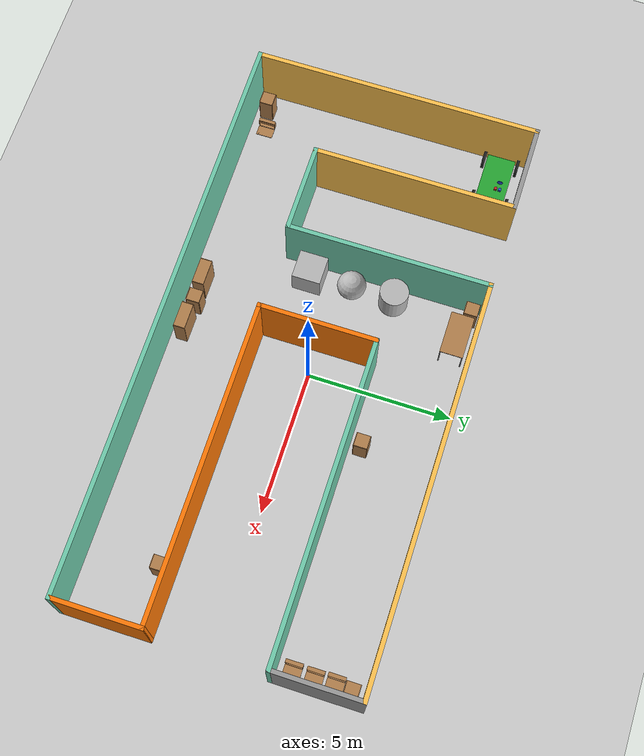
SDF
<sdf version="1.6">
 <world name="default">
  <light name="sun" type="directional">
   <pose>0 0 10 0 -0 0</pose>
   <diffuse>0.8 0.8 0.8 1</diffuse>
   <specular>0.2 0.2 0.2 1</specular>
   <attenuation>
    <range>1000</range>
    <constant>0.9</constant>
    <linear>0.01</linear>
    <quadratic>0.001</quadratic>
   </attenuation>
   <direction>-0.5 0.1 -0.9</direction>
  </light>
  <model name="ground_plane">
   <static>1</static>
   <link name="link">
    <collision name="collision">
     <geometry><plane><normal>0 0 1</normal><size>100 100</size></plane></geometry>
     <surface>
      <contact><collide_bitmask>65535</collide_bitmask></contact>
      <friction><ode><mu>100</mu><mu2>50</mu2></ode></friction>
     </surface>
    </collision>
    <visual name="visual">
     <cast_shadows>0</cast_shadows>
     <geometry><plane><normal>0 0 1</normal><size>100 100</size></plane></geometry>
     <material>
      <script><uri>file://media/materials/scripts/gazebo.material</uri><name>Gazebo/Grey</name></script>
     </material>
    </visual>
   </link>
  </model>
  <gravity>0 0 -9.8</gravity>
  <magnetic_field>6e-06 2.3e-05 -4.2e-05</magnetic_field>
  <atmosphere type="adiabatic"/>
  <physics name="default_physics" default="0" type="ode">
   <max_step_size>0.001</max_step_size>
   <real_time_factor>1</real_time_factor>
   <real_time_update_rate>1000</real_time_update_rate>
  </physics>
  <scene><ambient>0.4 0.4 0.4 1</ambient><background>0.7 0.7 0.7 1</background><shadows>1</shadows></scene>
  <spherical_coordinates>
   <surface_model>EARTH_WGS84</surface_model>
   <latitude_deg>0</latitude_deg>
   <longitude_deg>0</longitude_deg>
   <elevation>0</elevation>
   <heading_deg>0</heading_deg>
  </spherical_coordinates>
  <model name="simplebuilding">
   <link name="Wall_0">
    <collision name="Wall_0_Collision">
     <geometry><box><size>10.15 0.15 2.5</size></box></geometry>
     <pose>0 0 1.25 0 -0 0</pose>
    </collision>
    <visual name="Wall_0_Visual">
     <pose>0 0 1.25 0 -0 0</pose>
     <geometry><box><size>10.15 0.15 2.5</size></box></geometry>
     <material>
      <script><uri>file://media/materials/scripts/gazebo.material</uri><name>Gazebo/Grey</name></script>
      <ambient>1 0.764706 0.305882 1</ambient>
     </material>
     <meta><layer>0</layer></meta>
    </visual>
    <pose>-10 0 0 0 0 -1.5708</pose>
   </link>
   <link name="Wall_10">
    <collision name="Wall_10_Collision">
     <geometry><box><size>7.15 0.15 2.5</size></box></geometry>
     <pose>0 0 1.25 0 -0 0</pose>
    </collision>
    <visual name="Wall_10_Visual">
     <pose>0 0 1.25 0 -0 0</pose>
     <geometry><box><size>7.15 0.15 2.5</size></box></geometry>
     <material>
      <script><uri>file://media/materials/scripts/gazebo.material</uri><name>Gazebo/Grey</name></script>
      <ambient>0.435294 0.796078 0.67451 1</ambient>
     </material>
     <meta><layer>0</layer></meta>
    </visual>
    <pose>-4 1.5 0 0 -0 1.5708</pose>
   </link>
   <link name="Wall_12">
    <collision name="Wall_12_Collision">
     <geometry><box><size>14.15 0.15 2.5</size></box></geometry>
     <pose>0 0 1.25 0 -0 0</pose>
    </collision>
    <visual name="Wall_12_Visual">
     <pose>0 0 1.25 0 -0 0</pose>
     <geometry><box><size>14.15 0.15 2.5</size></box></geometry>
     <material>
      <script><uri>file://media/materials/scripts/gazebo.material</uri><name>Gazebo/Grey</name></script>
      <ambient>1 0.764706 0.305882 1</ambient>
     </material>
     <meta><layer>0</layer></meta>
    </visual>
    <pose>3 5 0 0 -0 0</pose>
   </link>
   <link name="Wall_13">
    <collision name="Wall_13_Collision">
     <geometry><box><size>3.15 0.15 2.5</size></box></geometry>
     <pose>0 0 1.25 0 -0 0</pose>
    </collision>
    <visual name="Wall_13_Visual">
     <pose>0 0 1.25 0 -0 0</pose>
     <geometry><box><size>3.15 0.15 2.5</size></box></geometry>
     <material>
      <script><uri>file://media/materials/scripts/gazebo.material</uri><name>Gazebo/Grey</name></script>
      <ambient>1 1 1 1</ambient>
     </material>
     <meta><layer>0</layer></meta>
    </visual>
    <pose>10 3.5 0 0 0 -1.5708</pose>
   </link>
   <link name="Wall_15">
    <collision name="Wall_15_Collision">
     <geometry><box><size>11.15 0.15 2.5</size></box></geometry>
     <pose>0 0 1.25 0 -0 0</pose>
    </collision>
    <visual name="Wall_15_Visual">
     <pose>0 0 1.25 0 -0 0</pose>
     <geometry><box><size>11.15 0.15 2.5</size></box></geometry>
     <material>
      <script><uri>file://media/materials/scripts/gazebo.material</uri><name>Gazebo/Grey</name></script>
      <ambient>0.435294 0.796078 0.67451 1</ambient>
     </material>
     <meta><layer>0</layer></meta>
    </visual>
    <pose>4.5 2 0 0 -0 3.14159</pose>
   </link>
   <link name="Wall_17">
    <collision name="Wall_17_Collision">
     <geometry><box><size>4.15 0.15 2.5</size></box></geometry>
     <pose>0 0 1.25 0 -0 0</pose>
    </collision>
    <visual name="Wall_17_Visual">
     <pose>0 0 1.25 0 -0 0</pose>
     <geometry><box><size>4.15 0.15 2.5</size></box></geometry>
     <material>
      <script><uri>file://media/materials/scripts/gazebo.material</uri><name>Gazebo/Grey</name></script>
      <ambient>0.996078 0.47451 0.0196078 1</ambient>
     </material>
     <meta><layer>0</layer></meta>
    </visual>
    <pose>-1 0 0 0 0 -1.5708</pose>
   </link>
   <link name="Wall_19">
    <collision name="Wall_19_Collision">
     <geometry><box><size>11.15 0.15 2.5</size></box></geometry>
     <pose>0 0 1.25 0 -0 0</pose>
    </collision>
    <visual name="Wall_19_Visual">
     <pose>0 0 1.25 0 -0 0</pose>
     <geometry><box><size>11.15 0.15 2.5</size></box></geometry>
     <material>
      <script><uri>file://media/materials/scripts/gazebo.material</uri><name>Gazebo/Grey</name></script>
      <ambient>0.996078 0.47451 0.0196078 1</ambient>
     </material>
     <meta><layer>0</layer></meta>
    </visual>
    <pose>4.5 -2 0 0 -0 0</pose>
   </link>
   <link name="Wall_2">
    <collision name="Wall_2_Collision">
     <geometry><box><size>20.15 0.15 2.5</size></box></geometry>
     <pose>0 0 1.25 0 -0 0</pose>
    </collision>
    <visual name="Wall_2_Visual">
     <pose>0 0 1.25 0 -0 0</pose>
     <geometry><box><size>20.15 0.15 2.5</size></box></geometry>
     <material>
      <script><uri>file://media/materials/scripts/gazebo.material</uri><name>Gazebo/Grey</name></script>
      <ambient>0.435294 0.796078 0.67451 1</ambient>
     </material>
     <meta><layer>0</layer></meta>
    </visual>
    <pose>0 -5 0 0 -0 0</pose>
   </link>
   <link name="Wall_21">
    <collision name="Wall_21_Collision">
     <geometry><box><size>3.15 0.15 2.5</size></box></geometry>
     <pose>0 0 1.25 0 -0 0</pose>
    </collision>
    <visual name="Wall_21_Visual">
     <pose>0 0 1.25 0 -0 0</pose>
     <geometry><box><size>3.15 0.15 2.5</size></box></geometry>
     <material>
      <script><uri>file://media/materials/scripts/gazebo.material</uri><name>Gazebo/Grey</name></script>
      <ambient>0.996078 0.47451 0.0196078 1</ambient>
     </material>
     <meta><layer>0</layer></meta>
    </visual>
    <pose>10 -3.5 0 0 0 -1.5708</pose>
   </link>
   <link name="Wall_4">
    <collision name="Wall_4_Collision">
     <geometry><box><size>3.15 0.15 2.5</size></box></geometry>
     <pose>0 0 1.25 0 -0 0</pose>
    </collision>
    <visual name="Wall_4_Visual">
     <pose>0 0 1.25 0 -0 0</pose>
     <geometry><box><size>3.15 0.15 2.5</size></box></geometry>
     <material>
      <script><uri>file://media/materials/scripts/gazebo.material</uri><name>Gazebo/Grey</name></script>
      <ambient>1 1 1 1</ambient>
     </material>
     <meta><layer>0</layer></meta>
    </visual>
    <pose>-8.5 5 0 0 -0 0</pose>
   </link>
   <link name="Wall_6">
    <collision name="Wall_6_Collision">
     <geometry><box><size>7.15 0.15 2.5</size></box></geometry>
     <pose>0 0 1.25 0 -0 0</pose>
    </collision>
    <visual name="Wall_6_Visual">
     <pose>0 0 1.25 0 -0 0</pose>
     <geometry><box><size>7.15 0.15 2.5</size></box></geometry>
     <material>
      <script><uri>file://media/materials/scripts/gazebo.material</uri><name>Gazebo/Grey</name></script>
      <ambient>1 0.764706 0.305882 1</ambient>
     </material>
     <meta><layer>0</layer></meta>
    </visual>
    <pose>-7 1.5 0 0 0 -1.5708</pose>
   </link>
   <link name="Wall_8">
    <collision name="Wall_8_Collision">
     <geometry><box><size>3.15 0.15 2.5</size></box></geometry>
     <pose>0 0 1.25 0 -0 0</pose>
    </collision>
    <visual name="Wall_8_Visual">
     <pose>0 0 1.25 0 -0 0</pose>
     <geometry><box><size>3.15 0.15 2.5</size></box></geometry>
     <material>
      <script><uri>file://media/materials/scripts/gazebo.material</uri><name>Gazebo/Grey</name></script>
      <ambient>0.435294 0.796078 0.67451 1</ambient>
     </material>
     <meta><layer>0</layer></meta>
    </visual>
    <pose>-5.5 -2 0 0 -0 0</pose>
   </link>
   <static>1</static>
  </model>
  <model name="cabinet">
   <static>1</static>
   <link name="cabinet_bottom_plate">
    <inertial>
     <pose>0 0 -1 0 -0 0</pose>
     <inertia><ixx>2.05</ixx><ixy>0</ixy><ixz>0</ixz><iyy>2.05</iyy><iyz>0</iyz><izz>2.05</izz></inertia>
     <mass>25</mass>
    </inertial>
    <collision name="cabinet_bottom_plate_geom">
     <pose>0 0 0.01 0 -0 0</pose>
     <geometry><box><size>0.45 0.45 0.02</size></box></geometry>
    </collision>
    <visual name="cabinet_bottom_plate_geom_visual">
     <pose>0 0 0.01 0 -0 0</pose>
     <geometry><box><size>0.45 0.45 0.02</size></box></geometry>
     <material>
      <script><uri>file://media/materials/scripts/gazebo.material</uri><name>Gazebo/Wood</name></script>
     </material>
    </visual>
    <collision name="cabinet_bottom_plate_geom_cabinet_back_plate">
     <pose>0.235 0 0.51 0 -0 0</pose>
     <geometry><box><size>0.02 0.45 1.02</size></box></geometry>
    </collision>
    <visual name="cabinet_bottom_plate_geom_cabinet_back_plate_visual">
     <pose>0.235 0 0.51 0 -0 0</pose>
     <geometry><box><size>0.02 0.45 1.02</size></box></geometry>
     <material>
      <script><uri>file://media/materials/scripts/gazebo.material</uri><name>Gazebo/Wood</name></script>
     </material>
    </visual>
    <collision name="cabinet_bottom_plate_geom_cabinet_left_plate">
     <pose>0 0.235 0.51 0 -0 0</pose>
     <geometry><box><size>0.45 0.02 1.02</size></box></geometry>
    </collision>
    <visual name="cabinet_bottom_plate_geom_cabinet_left_plate_visual">
     <pose>0 0.235 0.51 0 -0 0</pose>
     <geometry><box><size>0.45 0.02 1.02</size></box></geometry>
     <material>
      <script><uri>file://media/materials/scripts/gazebo.material</uri><name>Gazebo/Wood</name></script>
     </material>
    </visual>
    <collision name="cabinet_bottom_plate_geom_cabinet_middle_plate">
     <pose>0 0 0.51 0 -0 0</pose>
     <geometry><box><size>0.45 0.45 0.02</size></box></geometry>
    </collision>
    <visual name="cabinet_bottom_plate_geom_cabinet_middle_plate_visual">
     <pose>0 0 0.51 0 -0 0</pose>
     <geometry><box><size>0.45 0.45 0.02</size></box></geometry>
     <material>
      <script><uri>file://media/materials/scripts/gazebo.material</uri><name>Gazebo/Wood</name></script>
     </material>
    </visual>
    <collision name="cabinet_bottom_plate_geom_cabinet_right_plate">
     <pose>0 -0.235 0.51 0 -0 0</pose>
     <geometry><box><size>0.45 0.02 1.02</size></box></geometry>
    </collision>
    <visual name="cabinet_bottom_plate_geom_cabinet_right_plate_visual">
     <pose>0 -0.235 0.51 0 -0 0</pose>
     <geometry><box><size>0.45 0.02 1.02</size></box></geometry>
     <material>
      <script><uri>file://media/materials/scripts/gazebo.material</uri><name>Gazebo/Wood</name></script>
     </material>
    </visual>
    <collision name="cabinet_bottom_plate_geom_cabinet_top_plate">
     <pose>0 0 1.01 0 -0 0</pose>
     <geometry><box><size>0.45 0.45 0.02</size></box></geometry>
    </collision>
    <visual name="cabinet_bottom_plate_geom_cabinet_top_plate_visual">
     <pose>0 0 1.01 0 -0 0</pose>
     <geometry><box><size>0.45 0.45 0.02</size></box></geometry>
     <material>
      <script><uri>file://media/materials/scripts/gazebo.material</uri><name>Gazebo/Wood</name></script>
     </material>
    </visual>
   </link>
   <pose>-9.22504 -4.50417 0 0 -0 0</pose>
  </model>
  <model name="cabinet_0">
   <static>1</static>
   <link name="cabinet_bottom_plate">
    <inertial>
     <pose>0 0 -1 0 -0 0</pose>
     <inertia><ixx>2.05</ixx><ixy>0</ixy><ixz>0</ixz><iyy>2.05</iyy><iyz>0</iyz><izz>2.05</izz></inertia>
     <mass>25</mass>
    </inertial>
    <collision name="cabinet_bottom_plate_geom">
     <pose>0 0 0.01 0 -0 0</pose>
     <geometry><box><size>0.45 0.45 0.02</size></box></geometry>
    </collision>
    <visual name="cabinet_bottom_plate_geom_visual">
     <pose>0 0 0.01 0 -0 0</pose>
     <geometry><box><size>0.45 0.45 0.02</size></box></geometry>
     <material>
      <script><uri>file://media/materials/scripts/gazebo.material</uri><name>Gazebo/Wood</name></script>
     </material>
    </visual>
    <collision name="cabinet_bottom_plate_geom_cabinet_back_plate">
     <pose>0.235 0 0.51 0 -0 0</pose>
     <geometry><box><size>0.02 0.45 1.02</size></box></geometry>
    </collision>
    <visual name="cabinet_bottom_plate_geom_cabinet_back_plate_visual">
     <pose>0.235 0 0.51 0 -0 0</pose>
     <geometry><box><size>0.02 0.45 1.02</size></box></geometry>
     <material>
      <script><uri>file://media/materials/scripts/gazebo.material</uri><name>Gazebo/Wood</name></script>
     </material>
    </visual>
    <collision name="cabinet_bottom_plate_geom_cabinet_left_plate">
     <pose>0 0.235 0.51 0 -0 0</pose>
     <geometry><box><size>0.45 0.02 1.02</size></box></geometry>
    </collision>
    <visual name="cabinet_bottom_plate_geom_cabinet_left_plate_visual">
     <pose>0 0.235 0.51 0 -0 0</pose>
     <geometry><box><size>0.45 0.02 1.02</size></box></geometry>
     <material>
      <script><uri>file://media/materials/scripts/gazebo.material</uri><name>Gazebo/Wood</name></script>
     </material>
    </visual>
    <collision name="cabinet_bottom_plate_geom_cabinet_middle_plate">
     <pose>0 0 0.51 0 -0 0</pose>
     <geometry><box><size>0.45 0.45 0.02</size></box></geometry>
    </collision>
    <visual name="cabinet_bottom_plate_geom_cabinet_middle_plate_visual">
     <pose>0 0 0.51 0 -0 0</pose>
     <geometry><box><size>0.45 0.45 0.02</size></box></geometry>
     <material>
      <script><uri>file://media/materials/scripts/gazebo.material</uri><name>Gazebo/Wood</name></script>
     </material>
    </visual>
    <collision name="cabinet_bottom_plate_geom_cabinet_right_plate">
     <pose>0 -0.235 0.51 0 -0 0</pose>
     <geometry><box><size>0.45 0.02 1.02</size></box></geometry>
    </collision>
    <visual name="cabinet_bottom_plate_geom_cabinet_right_plate_visual">
     <pose>0 -0.235 0.51 0 -0 0</pose>
     <geometry><box><size>0.45 0.02 1.02</size></box></geometry>
     <material>
      <script><uri>file://media/materials/scripts/gazebo.material</uri><name>Gazebo/Wood</name></script>
     </material>
    </visual>
    <collision name="cabinet_bottom_plate_geom_cabinet_top_plate">
     <pose>0 0 1.01 0 -0 0</pose>
     <geometry><box><size>0.45 0.45 0.02</size></box></geometry>
    </collision>
    <visual name="cabinet_bottom_plate_geom_cabinet_top_plate_visual">
     <pose>0 0 1.01 0 -0 0</pose>
     <geometry><box><size>0.45 0.45 0.02</size></box></geometry>
     <material>
      <script><uri>file://media/materials/scripts/gazebo.material</uri><name>Gazebo/Wood</name></script>
     </material>
    </visual>
   </link>
   <pose>-3.62763 4.63881 0 0 -0 0</pose>
  </model>
  <model name="cabinet_1">
   <static>1</static>
   <link name="cabinet_bottom_plate">
    <inertial>
     <pose>0 0 -1 0 -0 0</pose>
     <inertia><ixx>2.05</ixx><ixy>0</ixy><ixz>0</ixz><iyy>2.05</iyy><iyz>0</iyz><izz>2.05</izz></inertia>
     <mass>25</mass>
    </inertial>
    <collision name="cabinet_bottom_plate_geom">
     <pose>0 0 0.01 0 -0 0</pose>
     <geometry><box><size>0.45 0.45 0.02</size></box></geometry>
    </collision>
    <visual name="cabinet_bottom_plate_geom_visual">
     <pose>0 0 0.01 0 -0 0</pose>
     <geometry><box><size>0.45 0.45 0.02</size></box></geometry>
     <material>
      <script><uri>file://media/materials/scripts/gazebo.material</uri><name>Gazebo/Wood</name></script>
     </material>
    </visual>
    <collision name="cabinet_bottom_plate_geom_cabinet_back_plate">
     <pose>0.235 0 0.51 0 -0 0</pose>
     <geometry><box><size>0.02 0.45 1.02</size></box></geometry>
    </collision>
    <visual name="cabinet_bottom_plate_geom_cabinet_back_plate_visual">
     <pose>0.235 0 0.51 0 -0 0</pose>
     <geometry><box><size>0.02 0.45 1.02</size></box></geometry>
     <material>
      <script><uri>file://media/materials/scripts/gazebo.material</uri><name>Gazebo/Wood</name></script>
     </material>
    </visual>
    <collision name="cabinet_bottom_plate_geom_cabinet_left_plate">
     <pose>0 0.235 0.51 0 -0 0</pose>
     <geometry><box><size>0.45 0.02 1.02</size></box></geometry>
    </collision>
    <visual name="cabinet_bottom_plate_geom_cabinet_left_plate_visual">
     <pose>0 0.235 0.51 0 -0 0</pose>
     <geometry><box><size>0.45 0.02 1.02</size></box></geometry>
     <material>
      <script><uri>file://media/materials/scripts/gazebo.material</uri><name>Gazebo/Wood</name></script>
     </material>
    </visual>
    <collision name="cabinet_bottom_plate_geom_cabinet_middle_plate">
     <pose>0 0 0.51 0 -0 0</pose>
     <geometry><box><size>0.45 0.45 0.02</size></box></geometry>
    </collision>
    <visual name="cabinet_bottom_plate_geom_cabinet_middle_plate_visual">
     <pose>0 0 0.51 0 -0 0</pose>
     <geometry><box><size>0.45 0.45 0.02</size></box></geometry>
     <material>
      <script><uri>file://media/materials/scripts/gazebo.material</uri><name>Gazebo/Wood</name></script>
     </material>
    </visual>
    <collision name="cabinet_bottom_plate_geom_cabinet_right_plate">
     <pose>0 -0.235 0.51 0 -0 0</pose>
     <geometry><box><size>0.45 0.02 1.02</size></box></geometry>
    </collision>
    <visual name="cabinet_bottom_plate_geom_cabinet_right_plate_visual">
     <pose>0 -0.235 0.51 0 -0 0</pose>
     <geometry><box><size>0.45 0.02 1.02</size></box></geometry>
     <material>
      <script><uri>file://media/materials/scripts/gazebo.material</uri><name>Gazebo/Wood</name></script>
     </material>
    </visual>
    <collision name="cabinet_bottom_plate_geom_cabinet_top_plate">
     <pose>0 0 1.01 0 -0 0</pose>
     <geometry><box><size>0.45 0.45 0.02</size></box></geometry>
    </collision>
    <visual name="cabinet_bottom_plate_geom_cabinet_top_plate_visual">
     <pose>0 0 1.01 0 -0 0</pose>
     <geometry><box><size>0.45 0.45 0.02</size></box></geometry>
     <material>
      <script><uri>file://media/materials/scripts/gazebo.material</uri><name>Gazebo/Wood</name></script>
     </material>
    </visual>
   </link>
   <pose>-1.22916 -4.44021 0 0 -0 0</pose>
  </model>
  <model name="cabinet_2">
   <static>1</static>
   <link name="cabinet_bottom_plate">
    <inertial>
     <pose>0 0 -1 0 -0 0</pose>
     <inertia><ixx>2.05</ixx><ixy>0</ixy><ixz>0</ixz><iyy>2.05</iyy><iyz>0</iyz><izz>2.05</izz></inertia>
     <mass>25</mass>
    </inertial>
    <collision name="cabinet_bottom_plate_geom">
     <pose>0 0 0.01 0 -0 0</pose>
     <geometry><box><size>0.45 0.45 0.02</size></box></geometry>
    </collision>
    <visual name="cabinet_bottom_plate_geom_visual">
     <pose>0 0 0.01 0 -0 0</pose>
     <geometry><box><size>0.45 0.45 0.02</size></box></geometry>
     <material>
      <script><uri>file://media/materials/scripts/gazebo.material</uri><name>Gazebo/Wood</name></script>
     </material>
    </visual>
    <collision name="cabinet_bottom_plate_geom_cabinet_back_plate">
     <pose>0.235 0 0.51 0 -0 0</pose>
     <geometry><box><size>0.02 0.45 1.02</size></box></geometry>
    </collision>
    <visual name="cabinet_bottom_plate_geom_cabinet_back_plate_visual">
     <pose>0.235 0 0.51 0 -0 0</pose>
     <geometry><box><size>0.02 0.45 1.02</size></box></geometry>
     <material>
      <script><uri>file://media/materials/scripts/gazebo.material</uri><name>Gazebo/Wood</name></script>
     </material>
    </visual>
    <collision name="cabinet_bottom_plate_geom_cabinet_left_plate">
     <pose>0 0.235 0.51 0 -0 0</pose>
     <geometry><box><size>0.45 0.02 1.02</size></box></geometry>
    </collision>
    <visual name="cabinet_bottom_plate_geom_cabinet_left_plate_visual">
     <pose>0 0.235 0.51 0 -0 0</pose>
     <geometry><box><size>0.45 0.02 1.02</size></box></geometry>
     <material>
      <script><uri>file://media/materials/scripts/gazebo.material</uri><name>Gazebo/Wood</name></script>
     </material>
    </visual>
    <collision name="cabinet_bottom_plate_geom_cabinet_middle_plate">
     <pose>0 0 0.51 0 -0 0</pose>
     <geometry><box><size>0.45 0.45 0.02</size></box></geometry>
    </collision>
    <visual name="cabinet_bottom_plate_geom_cabinet_middle_plate_visual">
     <pose>0 0 0.51 0 -0 0</pose>
     <geometry><box><size>0.45 0.45 0.02</size></box></geometry>
     <material>
      <script><uri>file://media/materials/scripts/gazebo.material</uri><name>Gazebo/Wood</name></script>
     </material>
    </visual>
    <collision name="cabinet_bottom_plate_geom_cabinet_right_plate">
     <pose>0 -0.235 0.51 0 -0 0</pose>
     <geometry><box><size>0.45 0.02 1.02</size></box></geometry>
    </collision>
    <visual name="cabinet_bottom_plate_geom_cabinet_right_plate_visual">
     <pose>0 -0.235 0.51 0 -0 0</pose>
     <geometry><box><size>0.45 0.02 1.02</size></box></geometry>
     <material>
      <script><uri>file://media/materials/scripts/gazebo.material</uri><name>Gazebo/Wood</name></script>
     </material>
    </visual>
    <collision name="cabinet_bottom_plate_geom_cabinet_top_plate">
     <pose>0 0 1.01 0 -0 0</pose>
     <geometry><box><size>0.45 0.45 0.02</size></box></geometry>
    </collision>
    <visual name="cabinet_bottom_plate_geom_cabinet_top_plate_visual">
     <pose>0 0 1.01 0 -0 0</pose>
     <geometry><box><size>0.45 0.45 0.02</size></box></geometry>
     <material>
      <script><uri>file://media/materials/scripts/gazebo.material</uri><name>Gazebo/Wood</name></script>
     </material>
    </visual>
   </link>
   <pose>9.61251 4.52482 0 0 -0 0</pose>
  </model>
  <model name="cabinet_3">
   <static>1</static>
   <link name="cabinet_bottom_plate">
    <inertial>
     <pose>0 0 -1 0 -0 0</pose>
     <inertia><ixx>2.05</ixx><ixy>0</ixy><ixz>0</ixz><iyy>2.05</iyy><iyz>0</iyz><izz>2.05</izz></inertia>
     <mass>25</mass>
    </inertial>
    <collision name="cabinet_bottom_plate_geom">
     <pose>0 0 0.01 0 -0 0</pose>
     <geometry><box><size>0.45 0.45 0.02</size></box></geometry>
    </collision>
    <visual name="cabinet_bottom_plate_geom_visual">
     <pose>0 0 0.01 0 -0 0</pose>
     <geometry><box><size>0.45 0.45 0.02</size></box></geometry>
     <material>
      <script><uri>file://media/materials/scripts/gazebo.material</uri><name>Gazebo/Wood</name></script>
     </material>
    </visual>
    <collision name="cabinet_bottom_plate_geom_cabinet_back_plate">
     <pose>0.235 0 0.51 0 -0 0</pose>
     <geometry><box><size>0.02 0.45 1.02</size></box></geometry>
    </collision>
    <visual name="cabinet_bottom_plate_geom_cabinet_back_plate_visual">
     <pose>0.235 0 0.51 0 -0 0</pose>
     <geometry><box><size>0.02 0.45 1.02</size></box></geometry>
     <material>
      <script><uri>file://media/materials/scripts/gazebo.material</uri><name>Gazebo/Wood</name></script>
     </material>
    </visual>
    <collision name="cabinet_bottom_plate_geom_cabinet_left_plate">
     <pose>0 0.235 0.51 0 -0 0</pose>
     <geometry><box><size>0.45 0.02 1.02</size></box></geometry>
    </collision>
    <visual name="cabinet_bottom_plate_geom_cabinet_left_plate_visual">
     <pose>0 0.235 0.51 0 -0 0</pose>
     <geometry><box><size>0.45 0.02 1.02</size></box></geometry>
     <material>
      <script><uri>file://media/materials/scripts/gazebo.material</uri><name>Gazebo/Wood</name></script>
     </material>
    </visual>
    <collision name="cabinet_bottom_plate_geom_cabinet_middle_plate">
     <pose>0 0 0.51 0 -0 0</pose>
     <geometry><box><size>0.45 0.45 0.02</size></box></geometry>
    </collision>
    <visual name="cabinet_bottom_plate_geom_cabinet_middle_plate_visual">
     <pose>0 0 0.51 0 -0 0</pose>
     <geometry><box><size>0.45 0.45 0.02</size></box></geometry>
     <material>
      <script><uri>file://media/materials/scripts/gazebo.material</uri><name>Gazebo/Wood</name></script>
     </material>
    </visual>
    <collision name="cabinet_bottom_plate_geom_cabinet_right_plate">
     <pose>0 -0.235 0.51 0 -0 0</pose>
     <geometry><box><size>0.45 0.02 1.02</size></box></geometry>
    </collision>
    <visual name="cabinet_bottom_plate_geom_cabinet_right_plate_visual">
     <pose>0 -0.235 0.51 0 -0 0</pose>
     <geometry><box><size>0.45 0.02 1.02</size></box></geometry>
     <material>
      <script><uri>file://media/materials/scripts/gazebo.material</uri><name>Gazebo/Wood</name></script>
     </material>
    </visual>
    <collision name="cabinet_bottom_plate_geom_cabinet_top_plate">
     <pose>0 0 1.01 0 -0 0</pose>
     <geometry><box><size>0.45 0.45 0.02</size></box></geometry>
    </collision>
    <visual name="cabinet_bottom_plate_geom_cabinet_top_plate_visual">
     <pose>0 0 1.01 0 -0 0</pose>
     <geometry><box><size>0.45 0.45 0.02</size></box></geometry>
     <material>
      <script><uri>file://media/materials/scripts/gazebo.material</uri><name>Gazebo/Wood</name></script>
     </material>
    </visual>
   </link>
   <pose>1.94004 2.47429 0 0 -0 0</pose>
  </model>
  <model name="cabinet_4">
   <static>1</static>
   <link name="cabinet_bottom_plate">
    <inertial>
     <pose>0 0 -1 0 -0 0</pose>
     <inertia><ixx>2.05</ixx><ixy>0</ixy><ixz>0</ixz><iyy>2.05</iyy><iyz>0</iyz><izz>2.05</izz></inertia>
     <mass>25</mass>
    </inertial>
    <collision name="cabinet_bottom_plate_geom">
     <pose>0 0 0.01 0 -0 0</pose>
     <geometry><box><size>0.45 0.45 0.02</size></box></geometry>
    </collision>
    <visual name="cabinet_bottom_plate_geom_visual">
     <pose>0 0 0.01 0 -0 0</pose>
     <geometry><box><size>0.45 0.45 0.02</size></box></geometry>
     <material>
      <script><uri>file://media/materials/scripts/gazebo.material</uri><name>Gazebo/Wood</name></script>
     </material>
    </visual>
    <collision name="cabinet_bottom_plate_geom_cabinet_back_plate">
     <pose>0.235 0 0.51 0 -0 0</pose>
     <geometry><box><size>0.02 0.45 1.02</size></box></geometry>
    </collision>
    <visual name="cabinet_bottom_plate_geom_cabinet_back_plate_visual">
     <pose>0.235 0 0.51 0 -0 0</pose>
     <geometry><box><size>0.02 0.45 1.02</size></box></geometry>
     <material>
      <script><uri>file://media/materials/scripts/gazebo.material</uri><name>Gazebo/Wood</name></script>
     </material>
    </visual>
    <collision name="cabinet_bottom_plate_geom_cabinet_left_plate">
     <pose>0 0.235 0.51 0 -0 0</pose>
     <geometry><box><size>0.45 0.02 1.02</size></box></geometry>
    </collision>
    <visual name="cabinet_bottom_plate_geom_cabinet_left_plate_visual">
     <pose>0 0.235 0.51 0 -0 0</pose>
     <geometry><box><size>0.45 0.02 1.02</size></box></geometry>
     <material>
      <script><uri>file://media/materials/scripts/gazebo.material</uri><name>Gazebo/Wood</name></script>
     </material>
    </visual>
    <collision name="cabinet_bottom_plate_geom_cabinet_middle_plate">
     <pose>0 0 0.51 0 -0 0</pose>
     <geometry><box><size>0.45 0.45 0.02</size></box></geometry>
    </collision>
    <visual name="cabinet_bottom_plate_geom_cabinet_middle_plate_visual">
     <pose>0 0 0.51 0 -0 0</pose>
     <geometry><box><size>0.45 0.45 0.02</size></box></geometry>
     <material>
      <script><uri>file://media/materials/scripts/gazebo.material</uri><name>Gazebo/Wood</name></script>
     </material>
    </visual>
    <collision name="cabinet_bottom_plate_geom_cabinet_right_plate">
     <pose>0 -0.235 0.51 0 -0 0</pose>
     <geometry><box><size>0.45 0.02 1.02</size></box></geometry>
    </collision>
    <visual name="cabinet_bottom_plate_geom_cabinet_right_plate_visual">
     <pose>0 -0.235 0.51 0 -0 0</pose>
     <geometry><box><size>0.45 0.02 1.02</size></box></geometry>
     <material>
      <script><uri>file://media/materials/scripts/gazebo.material</uri><name>Gazebo/Wood</name></script>
     </material>
    </visual>
    <collision name="cabinet_bottom_plate_geom_cabinet_top_plate">
     <pose>0 0 1.01 0 -0 0</pose>
     <geometry><box><size>0.45 0.45 0.02</size></box></geometry>
    </collision>
    <visual name="cabinet_bottom_plate_geom_cabinet_top_plate_visual">
     <pose>0 0 1.01 0 -0 0</pose>
     <geometry><box><size>0.45 0.45 0.02</size></box></geometry>
     <material>
      <script><uri>file://media/materials/scripts/gazebo.material</uri><name>Gazebo/Wood</name></script>
     </material>
    </visual>
   </link>
   <pose>7.75208 -2.44223 0 0 -0 0</pose>
  </model>
  <model name="table">
   <static>1</static>
   <link name="link">
    <collision name="surface">
     <pose>0 0 1 0 -0 0</pose>
     <geometry><box><size>1.5 0.8 0.03</size></box></geometry>
     <surface><friction><ode><mu>0.6</mu><mu2>0.6</mu2></ode></friction></surface>
    </collision>
    <visual name="visual1">
     <pose>0 0 1 0 -0 0</pose>
     <geometry><box><size>1.5 0.8 0.03</size></box></geometry>
     <material>
      <script><uri>file://media/materials/scripts/gazebo.material</uri><name>Gazebo/Wood</name></script>
     </material>
    </visual>
    <collision name="front_left_leg">
     <pose>0.68 0.38 0.5 0 -0 0</pose>
     <geometry><cylinder><radius>0.02</radius><length>1</length></cylinder></geometry>
    </collision>
    <visual name="front_left_leg">
     <pose>0.68 0.38 0.5 0 -0 0</pose>
     <geometry><cylinder><radius>0.02</radius><length>1</length></cylinder></geometry>
     <material>
      <script><uri>file://media/materials/scripts/gazebo.material</uri><name>Gazebo/Grey</name></script>
     </material>
    </visual>
    <collision name="front_right_leg">
     <pose>0.68 -0.38 0.5 0 -0 0</pose>
     <geometry><cylinder><radius>0.02</radius><length>1</length></cylinder></geometry>
    </collision>
    <visual name="front_right_leg">
     <pose>0.68 -0.38 0.5 0 -0 0</pose>
     <geometry><cylinder><radius>0.02</radius><length>1</length></cylinder></geometry>
     <material>
      <script><uri>file://media/materials/scripts/gazebo.material</uri><name>Gazebo/Grey</name></script>
     </material>
    </visual>
    <collision name="back_right_leg">
     <pose>-0.68 -0.38 0.5 0 -0 0</pose>
     <geometry><cylinder><radius>0.02</radius><length>1</length></cylinder></geometry>
    </collision>
    <visual name="back_right_leg">
     <pose>-0.68 -0.38 0.5 0 -0 0</pose>
     <geometry><cylinder><radius>0.02</radius><length>1</length></cylinder></geometry>
     <material>
      <script><uri>file://media/materials/scripts/gazebo.material</uri><name>Gazebo/Grey</name></script>
     </material>
    </visual>
    <collision name="back_left_leg">
     <pose>-0.68 0.38 0.5 0 -0 0</pose>
     <geometry><cylinder><radius>0.02</radius><length>1</length></cylinder></geometry>
    </collision>
    <visual name="back_left_leg">
     <pose>-0.68 0.38 0.5 0 -0 0</pose>
     <geometry><cylinder><radius>0.02</radius><length>1</length></cylinder></geometry>
     <material>
      <script><uri>file://media/materials/scripts/gazebo.material</uri><name>Gazebo/Grey</name></script>
     </material>
    </visual>
   </link>
   <pose>-2.57486 4.40862 0 0 -0 0</pose>
  </model>
  <model name="car">
   <link name="chassis">
    <pose>0 0 0.3 0 -0 0</pose>
    <collision name="collision"><geometry><box><size>2 1 0.2</size></box></geometry></collision>
    <visual name="visual">
     <geometry><box><size>2 1 0.2</size></box></geometry>
     <material>
      <script><uri>file://media/materials/scripts/gazebo.material</uri><name>Gazebo/Green</name></script>
     </material>
    </visual>
    <inertial>
     <inertia><ixx>1</ixx><ixy>0</ixy><ixz>0</ixz><iyy>1</iyy><iyz>0</iyz><izz>1</izz></inertia>
     <mass>1</mass>
    </inertial>
   </link>
   <link name="front_left_wheel">
    <pose>0.8 0.6 0.3 -0 1.5707 1.5707</pose>
    <collision name="collision">
     <geometry><cylinder><radius>0.3</radius><length>0.1</length></cylinder></geometry>
    </collision>
    <visual name="visual">
     <geometry><cylinder><radius>0.3</radius><length>0.1</length></cylinder></geometry>
     <material>
      <script><uri>file://media/materials/scripts/gazebo.material</uri><name>Gazebo/Black</name></script>
     </material>
    </visual>
    <inertial>
     <inertia><ixx>1</ixx><ixy>0</ixy><ixz>0</ixz><iyy>1</iyy><iyz>0</iyz><izz>1</izz></inertia>
     <mass>1</mass>
    </inertial>
   </link>
   <link name="front_right_wheel">
    <pose>0.8 -0.6 0.3 -0 1.5707 1.5707</pose>
    <collision name="collision">
     <geometry><cylinder><radius>0.3</radius><length>0.1</length></cylinder></geometry>
    </collision>
    <visual name="visual">
     <geometry><cylinder><radius>0.3</radius><length>0.1</length></cylinder></geometry>
     <material>
      <script><uri>file://media/materials/scripts/gazebo.material</uri><name>Gazebo/Black</name></script>
     </material>
    </visual>
    <inertial>
     <inertia><ixx>1</ixx><ixy>0</ixy><ixz>0</ixz><iyy>1</iyy><iyz>0</iyz><izz>1</izz></inertia>
     <mass>1</mass>
    </inertial>
   </link>
   <link name="back_right_wheel">
    <pose>-0.8 -0.6 0.3 -0 1.5707 1.5707</pose>
    <collision name="collision">
     <geometry><cylinder><radius>0.3</radius><length>0.1</length></cylinder></geometry>
    </collision>
    <visual name="visual">
     <geometry><cylinder><radius>0.3</radius><length>0.1</length></cylinder></geometry>
     <material>
      <script><uri>file://media/materials/scripts/gazebo.material</uri><name>Gazebo/Black</name></script>
     </material>
    </visual>
    <inertial>
     <inertia><ixx>1</ixx><ixy>0</ixy><ixz>0</ixz><iyy>1</iyy><iyz>0</iyz><izz>1</izz></inertia>
     <mass>1</mass>
    </inertial>
   </link>
   <link name="back_left_wheel">
    <pose>-0.8 0.6 0.3 -0 1.5707 1.5707</pose>
    <collision name="collision">
     <geometry><cylinder><radius>0.3</radius><length>0.1</length></cylinder></geometry>
    </collision>
    <visual name="visual">
     <geometry><cylinder><radius>0.3</radius><length>0.1</length></cylinder></geometry>
     <material>
      <script><uri>file://media/materials/scripts/gazebo.material</uri><name>Gazebo/Black</name></script>
     </material>
    </visual>
    <inertial>
     <inertia><ixx>1</ixx><ixy>0</ixy><ixz>0</ixz><iyy>1</iyy><iyz>0</iyz><izz>1</izz></inertia>
     <mass>1</mass>
    </inertial>
   </link>
   <link name="gas_pedal">
    <pose>0.3 0.1 0.5 0 -0 0</pose>
    <collision name="collision"><geometry><box><size>0.1 0.1 0.1</size></box></geometry></collision>
    <visual name="visual">
     <geometry><box><size>0.1 0.1 0.1</size></box></geometry>
     <material>
      <script><uri>file://media/materials/scripts/gazebo.material</uri><name>Gazebo/Red</name></script>
     </material>
    </visual>
    <inertial>
     <inertia><ixx>1</ixx><ixy>0</ixy><ixz>0</ixz><iyy>1</iyy><iyz>0</iyz><izz>1</izz></inertia>
     <mass>1</mass>
    </inertial>
   </link>
   <link name="brake_pedal">
    <pose>0.3 0.25 0.5 0 -0 0</pose>
    <collision name="collision"><geometry><box><size>0.1 0.1 0.1</size></box></geometry></collision>
    <visual name="visual">
     <geometry><box><size>0.1 0.1 0.1</size></box></geometry>
     <material>
      <script><uri>file://media/materials/scripts/gazebo.material</uri><name>Gazebo/Blue</name></script>
     </material>
    </visual>
    <inertial>
     <inertia><ixx>1</ixx><ixy>0</ixy><ixz>0</ixz><iyy>1</iyy><iyz>0</iyz><izz>1</izz></inertia>
     <mass>1</mass>
    </inertial>
   </link>
   <link name="steering_wheel">
    <pose>0.3 0.2 1 0 1.5707 0</pose>
    <collision name="collision">
     <geometry><cylinder><radius>0.1</radius><length>0.01</length></cylinder></geometry>
    </collision>
    <visual name="visual">
     <geometry><cylinder><radius>0.1</radius><length>0.01</length></cylinder></geometry>
     <material>
      <script><uri>file://media/materials/scripts/gazebo.material</uri><name>Gazebo/Blue</name></script>
     </material>
    </visual>
    <inertial>
     <inertia><ixx>1</ixx><ixy>0</ixy><ixz>0</ixz><iyy>1</iyy><iyz>0</iyz><izz>1</izz></inertia>
     <mass>1</mass>
    </inertial>
   </link>
   <joint name="gas_joint" type="prismatic">
    <parent>chassis</parent>
    <child>gas_pedal</child>
    <axis>
     <xyz>1 0 0</xyz>
     <limit><lower>0</lower><upper>0.2</upper></limit>
     <use_parent_model_frame>1</use_parent_model_frame>
     <dynamics><spring_reference>0</spring_reference><spring_stiffness>0</spring_stiffness></dynamics>
    </axis>
   </joint>
   <joint name="brake_joint" type="prismatic">
    <parent>chassis</parent>
    <child>brake_pedal</child>
    <axis>
     <xyz>1 0 0</xyz>
     <limit><lower>0</lower><upper>0.2</upper></limit>
     <use_parent_model_frame>1</use_parent_model_frame>
     <dynamics><spring_reference>0</spring_reference><spring_stiffness>0</spring_stiffness></dynamics>
    </axis>
   </joint>
   <joint name="steering_joint" type="revolute">
    <parent>chassis</parent>
    <child>steering_wheel</child>
    <axis>
     <xyz>1 0 0</xyz>
     <limit><lower>-7.853</lower><upper>7.853</upper></limit>
     <use_parent_model_frame>1</use_parent_model_frame>
     <dynamics><spring_reference>0</spring_reference><spring_stiffness>0</spring_stiffness></dynamics>
    </axis>
   </joint>
   <joint name="front_left_joint" type="revolute2">
    <parent>chassis</parent>
    <child>front_left_wheel</child>
    <axis>
     <xyz>0 0 1</xyz>
     <limit><lower>8.59665e-06</lower><upper>8.59665e-06</upper></limit>
     <use_parent_model_frame>1</use_parent_model_frame>
     <dynamics><spring_reference>0</spring_reference><spring_stiffness>0</spring_stiffness></dynamics>
    </axis>
    <axis2>
     <xyz>0 1 0</xyz>
     <use_parent_model_frame>1</use_parent_model_frame>
     <dynamics><spring_reference>0</spring_reference><spring_stiffness>0</spring_stiffness></dynamics>
    </axis2>
    <physics><ode><limit><cfm>0</cfm><erp>0.9</erp></limit></ode></physics>
   </joint>
   <joint name="front_right_joint" type="revolute2">
    <parent>chassis</parent>
    <child>front_right_wheel</child>
    <axis>
     <xyz>0 0 1</xyz>
     <limit><lower>8.59665e-06</lower><upper>8.59665e-06</upper></limit>
     <use_parent_model_frame>1</use_parent_model_frame>
     <dynamics><spring_reference>0</spring_reference><spring_stiffness>0</spring_stiffness></dynamics>
    </axis>
    <axis2>
     <xyz>0 1 0</xyz>
     <use_parent_model_frame>1</use_parent_model_frame>
     <dynamics><spring_reference>0</spring_reference><spring_stiffness>0</spring_stiffness></dynamics>
    </axis2>
    <physics><ode><limit><cfm>0</cfm><erp>0.9</erp></limit></ode></physics>
   </joint>
   <joint name="back_right_joint" type="revolute2">
    <parent>chassis</parent>
    <child>back_right_wheel</child>
    <axis>
     <xyz>0 0 1</xyz>
     <limit><lower>0</lower><upper>0</upper></limit>
     <use_parent_model_frame>1</use_parent_model_frame>
     <dynamics><spring_reference>0</spring_reference><spring_stiffness>0</spring_stiffness></dynamics>
    </axis>
    <axis2>
     <xyz>0 1 0</xyz>
     <use_parent_model_frame>1</use_parent_model_frame>
     <dynamics><spring_reference>0</spring_reference><spring_stiffness>0</spring_stiffness></dynamics>
    </axis2>
    <physics><ode><limit><cfm>0</cfm><erp>0.9</erp></limit></ode></physics>
   </joint>
   <joint name="back_left_joint" type="revolute2">
    <parent>chassis</parent>
    <child>back_left_wheel</child>
    <axis>
     <xyz>0 0 1</xyz>
     <limit><lower>0</lower><upper>0</upper></limit>
     <use_parent_model_frame>1</use_parent_model_frame>
     <dynamics><spring_reference>0</spring_reference><spring_stiffness>0</spring_stiffness></dynamics>
    </axis>
    <axis2>
     <xyz>0 1 0</xyz>
     <use_parent_model_frame>1</use_parent_model_frame>
     <dynamics><spring_reference>0</spring_reference><spring_stiffness>0</spring_stiffness></dynamics>
    </axis2>
    <physics><ode><limit><cfm>0</cfm><erp>0.9</erp></limit></ode></physics>
   </joint>
   <plugin name="vehicle" filename="libVehiclePlugin.so">
    <front_left>front_left_joint</front_left>
    <front_right>front_right_joint</front_right>
    <back_left>back_left_joint</back_left>
    <back_right>back_right_joint</back_right>
    <gas>gas_joint</gas>
    <brake>brake_joint</brake>
    <steering>steering_joint</steering>
    <front_power>10</front_power>
    <rear_power>10</rear_power>
    <tire_angle_range>0.5</tire_angle_range>
    <max_speed>10</max_speed>
    <aero_load>0.1</aero_load>
   </plugin>
   <pose>-8.8251 4.08357 -0.002615 -0.000273 0.000907 0.000236</pose>
  </model>
  <model name="textured_shapes">
   <pose>-3.42499 0.460971 0.5 0 -0 3e-06</pose>
   <link name="box">
    <pose>0 -1.5 0 0 -0 0</pose>
    <collision name="collision"><geometry><box><size>1 1 1</size></box></geometry></collision>
    <visual name="visual">
     <geometry><box><size>1 1 1</size></box></geometry>
     <material>
      <script>
       <uri>model://textured_shapes/materials/scripts</uri>
       <uri>model://textured_shapes/materials/textures</uri>
       <name>TexturedShape/Squares</name>
      </script>
     </material>
    </visual>
    <inertial>
     <inertia><ixx>1</ixx><ixy>0</ixy><ixz>0</ixz><iyy>1</iyy><iyz>0</iyz><izz>1</izz></inertia>
     <mass>1</mass>
    </inertial>
   </link>
   <link name="sphere">
    <collision name="collision"><geometry><sphere><radius>0.5</radius></sphere></geometry></collision>
    <visual name="visual">
     <geometry><sphere><radius>0.5</radius></sphere></geometry>
     <material>
      <script>
       <uri>model://textured_shapes/materials/scripts</uri>
       <uri>model://textured_shapes/materials/textures</uri>
       <name>TexturedShape/Squares</name>
      </script>
     </material>
    </visual>
    <inertial>
     <inertia><ixx>1</ixx><ixy>0</ixy><ixz>0</ixz><iyy>1</iyy><iyz>0</iyz><izz>1</izz></inertia>
     <mass>1</mass>
    </inertial>
   </link>
   <link name="cylinder">
    <pose>0 1.5 0 0 -0 0</pose>
    <collision name="collision">
     <geometry><cylinder><radius>0.5</radius><length>1</length></cylinder></geometry>
    </collision>
    <visual name="visual">
     <geometry><cylinder><radius>0.5</radius><length>1</length></cylinder></geometry>
     <material>
      <script>
       <uri>model://textured_shapes/materials/scripts</uri>
       <uri>model://textured_shapes/materials/textures</uri>
       <name>TexturedShape/Squares</name>
      </script>
     </material>
    </visual>
    <inertial>
     <inertia><ixx>1</ixx><ixy>0</ixy><ixz>0</ixz><iyy>1</iyy><iyz>0</iyz><izz>1</izz></inertia>
     <mass>1</mass>
    </inertial>
   </link>
  </model>
  <model name="wooden_case">
   <link name="base">
    <pose>0 0 0.024 0 -0 0</pose>
    <inertial>
     <pose>-0.022184 0 0.171592 0 -0 0</pose>
     <mass>3.96264</mass>
     <inertia>
      <ixx>0.213536</ixx>
      <ixy>0</ixy>
      <ixz>0.000779377</ixz>
      <iyy>0.0708943</iyy>
      <iyz>0</iyz>
      <izz>0.154604</izz>
     </inertia>
    </inertial>
    <collision name="collision_back">
     <pose>-0.053975 0 0.1778 0 -0 0</pose>
     <geometry><box><size>0.01905 0.5461 0.3175</size></box></geometry>
     <surface>
      <contact>
       <poissons_ratio>0.347</poissons_ratio>
       <elastic_modulus>8.8e+09</elastic_modulus>
       <ode><kp>100000</kp><kd>100</kd><max_vel>100</max_vel><min_depth>0.001</min_depth></ode>
      </contact>
      <friction>
       <torsional>
        <coefficient>1</coefficient>
        <use_patch_radius>0</use_patch_radius>
        <surface_radius>0.01</surface_radius>
       </torsional>
      </friction>
     </surface>
    </collision>
    <visual name="visual_back">
     <pose>-0.053975 0 0.1778 0 -0 0</pose>
     <geometry><box><size>0.01905 0.5461 0.3175</size></box></geometry>
     <material>
      <script><uri>file://media/materials/scripts/gazebo.material</uri><name>Gazebo/Wood</name></script>
     </material>
    </visual>
    <collision name="collision_bottom">
     <pose>0 0 0.009525 0 -0 0</pose>
     <geometry><box><size>0.127 0.5842 0.01905</size></box></geometry>
     <surface>
      <contact>
       <poissons_ratio>0.347</poissons_ratio>
       <elastic_modulus>8.8e+09</elastic_modulus>
       <ode><kp>100000</kp><kd>100</kd><max_vel>100</max_vel><min_depth>0.001</min_depth></ode>
      </contact>
      <friction>
       <torsional>
        <coefficient>1</coefficient>
        <use_patch_radius>0</use_patch_radius>
        <surface_radius>0.01</surface_radius>
       </torsional>
      </friction>
     </surface>
    </collision>
    <visual name="visual_bottom">
     <pose>0 0 0.009525 0 -0 0</pose>
     <geometry><box><size>0.127 0.5842 0.01905</size></box></geometry>
     <material>
      <script><uri>file://media/materials/scripts/gazebo.material</uri><name>Gazebo/Wood</name></script>
     </material>
    </visual>
    <collision name="collision_top">
     <pose>0 0 0.346075 0 -0 0</pose>
     <geometry><box><size>0.127 0.5842 0.01905</size></box></geometry>
     <surface>
      <contact>
       <poissons_ratio>0.347</poissons_ratio>
       <elastic_modulus>8.8e+09</elastic_modulus>
       <ode><kp>100000</kp><kd>100</kd><max_vel>100</max_vel><min_depth>0.001</min_depth></ode>
      </contact>
      <friction>
       <torsional>
        <coefficient>1</coefficient>
        <use_patch_radius>0</use_patch_radius>
        <surface_radius>0.01</surface_radius>
       </torsional>
      </friction>
     </surface>
    </collision>
    <visual name="visual_top">
     <pose>0 0 0.346075 0 -0 0</pose>
     <geometry><box><size>0.127 0.5842 0.01905</size></box></geometry>
     <material>
      <script><uri>file://media/materials/scripts/gazebo.material</uri><name>Gazebo/Wood</name></script>
     </material>
    </visual>
    <collision name="collision_left">
     <pose>0 -0.282575 0.1778 0 -0 0</pose>
     <geometry><box><size>0.127 0.01905 0.3175</size></box></geometry>
     <surface>
      <contact>
       <poissons_ratio>0.347</poissons_ratio>
       <elastic_modulus>8.8e+09</elastic_modulus>
       <ode><kp>100000</kp><kd>100</kd><max_vel>100</max_vel><min_depth>0.001</min_depth></ode>
      </contact>
      <friction>
       <torsional>
        <coefficient>1</coefficient>
        <use_patch_radius>0</use_patch_radius>
        <surface_radius>0.01</surface_radius>
       </torsional>
      </friction>
     </surface>
    </collision>
    <visual name="visual_left">
     <pose>0 -0.282575 0.1778 0 -0 0</pose>
     <geometry><box><size>0.127 0.01905 0.3175</size></box></geometry>
     <material>
      <script><uri>file://media/materials/scripts/gazebo.material</uri><name>Gazebo/Wood</name></script>
     </material>
    </visual>
    <collision name="collision_right">
     <pose>0 0.282575 0.1778 0 -0 0</pose>
     <geometry><box><size>0.127 0.01905 0.3175</size></box></geometry>
     <surface>
      <contact>
       <poissons_ratio>0.347</poissons_ratio>
       <elastic_modulus>8.8e+09</elastic_modulus>
       <ode><kp>100000</kp><kd>100</kd><max_vel>100</max_vel><min_depth>0.001</min_depth></ode>
      </contact>
      <friction>
       <torsional>
        <coefficient>1</coefficient>
        <use_patch_radius>0</use_patch_radius>
        <surface_radius>0.01</surface_radius>
       </torsional>
      </friction>
     </surface>
    </collision>
    <visual name="visual_right">
     <pose>0 0.282575 0.1778 0 -0 0</pose>
     <geometry><box><size>0.127 0.01905 0.3175</size></box></geometry>
     <material>
      <script><uri>file://media/materials/scripts/gazebo.material</uri><name>Gazebo/Wood</name></script>
     </material>
    </visual>
    <collision name="collision_block_left">
     <pose>0.0095 -0.2151 -0.012 0 -0 0</pose>
     <geometry><box><size>0.108 0.05 0.024</size></box></geometry>
     <surface>
      <contact>
       <poissons_ratio>0.347</poissons_ratio>
       <elastic_modulus>8.8e+09</elastic_modulus>
       <ode><kp>100000</kp><kd>100</kd><max_vel>100</max_vel><min_depth>0.001</min_depth></ode>
      </contact>
      <friction>
       <torsional>
        <coefficient>1</coefficient>
        <use_patch_radius>0</use_patch_radius>
        <surface_radius>0.01</surface_radius>
       </torsional>
      </friction>
     </surface>
    </collision>
    <visual name="visual_block_left">
     <pose>0.0095 -0.2151 -0.012 0 -0 0</pose>
     <geometry><box><size>0.108 0.05 0.024</size></box></geometry>
     <material>
      <script><uri>file://media/materials/scripts/gazebo.material</uri><name>Gazebo/Wood</name></script>
     </material>
    </visual>
    <collision name="collision_block_right">
     <pose>0.0095 0.2151 -0.012 0 -0 0</pose>
     <geometry><box><size>0.108 0.05 0.024</size></box></geometry>
     <surface>
      <contact>
       <poissons_ratio>0.347</poissons_ratio>
       <elastic_modulus>8.8e+09</elastic_modulus>
       <ode><kp>100000</kp><kd>100</kd><max_vel>100</max_vel><min_depth>0.001</min_depth></ode>
      </contact>
      <friction>
       <torsional>
        <coefficient>1</coefficient>
        <use_patch_radius>0</use_patch_radius>
        <surface_radius>0.01</surface_radius>
       </torsional>
      </friction>
     </surface>
    </collision>
    <visual name="visual_block_right">
     <pose>0.0095 0.2151 -0.012 0 -0 0</pose>
     <geometry><box><size>0.108 0.05 0.024</size></box></geometry>
     <material>
      <script><uri>file://media/materials/scripts/gazebo.material</uri><name>Gazebo/Wood</name></script>
     </material>
    </visual>
   </link>
   <link name="lid">
    <pose>0.243775 0 0.009525 0 -0 0</pose>
    <inertial>
     <mass>1.97874</mass>
     <inertia>
      <ixx>0.0563367</ixx>
      <ixy>0</ixy>
      <ixz>0</ixz>
      <iyy>0.020911</iyy>
      <iyz>0</iyz>
      <izz>0.0771281</izz>
     </inertia>
    </inertial>
    <collision name="collision">
     <geometry><box><size>0.3556 0.5842 0.01905</size></box></geometry>
     <surface>
      <contact>
       <poissons_ratio>0.347</poissons_ratio>
       <elastic_modulus>8.8e+09</elastic_modulus>
       <ode><kp>100000</kp><kd>100</kd><max_vel>100</max_vel><min_depth>0.001</min_depth></ode>
      </contact>
      <friction>
       <torsional>
        <coefficient>1</coefficient>
        <use_patch_radius>0</use_patch_radius>
        <surface_radius>0.01</surface_radius>
       </torsional>
      </friction>
     </surface>
    </collision>
    <visual name="visual">
     <geometry><box><size>0.3556 0.5842 0.01905</size></box></geometry>
     <material>
      <script><uri>file://media/materials/scripts/gazebo.material</uri><name>Gazebo/Wood</name></script>
     </material>
    </visual>
    <visual name="tee_nut_1">
     <pose>0.122 -0.216 0 0 -0 0</pose>
     <geometry><cylinder><radius>0.00635</radius><length>0.0192405</length></cylinder></geometry>
     <material>
      <script><uri>file://media/materials/scripts/gazebo.material</uri><name>Gazebo/Grey</name></script>
     </material>
    </visual>
    <visual name="tee_nut_2">
     <pose>0.122 -0.088 0 0 -0 0</pose>
     <geometry><cylinder><radius>0.00635</radius><length>0.0192405</length></cylinder></geometry>
     <material>
      <script><uri>file://media/materials/scripts/gazebo.material</uri><name>Gazebo/Grey</name></script>
     </material>
    </visual>
    <visual name="tee_nut_3">
     <pose>0.122 0.088 0 0 -0 0</pose>
     <geometry><cylinder><radius>0.00635</radius><length>0.0192405</length></cylinder></geometry>
     <material>
      <script><uri>file://media/materials/scripts/gazebo.material</uri><name>Gazebo/Grey</name></script>
     </material>
    </visual>
    <visual name="tee_nut_4">
     <pose>0.122 0.216 0 0 -0 0</pose>
     <geometry><cylinder><radius>0.00635</radius><length>0.0192405</length></cylinder></geometry>
     <material>
      <script><uri>file://media/materials/scripts/gazebo.material</uri><name>Gazebo/Grey</name></script>
     </material>
    </visual>
   </link>
   <joint name="lid_hinge" type="revolute">
    <pose>-0.1778 0 0.01905 0 -0 0</pose>
    <parent>base</parent>
    <child>lid</child>
    <axis>
     <xyz>0 1 0</xyz>
     <limit><upper>0.523599</upper><lower>-1.5708</lower></limit>
     <use_parent_model_frame>0</use_parent_model_frame>
     <dynamics><spring_reference>0</spring_reference><spring_stiffness>0</spring_stiffness></dynamics>
    </axis>
   </joint>
   <pose>-8.68992 -4.36219 -0.001057 0 -0.000429 0</pose>
  </model>
  <model name="bookshelf">
   <static>1</static>
   <link name="link">
    <inertial><mass>1</mass></inertial>
    <collision name="back">
     <pose>0 0.005 0.6 0 -0 0</pose>
     <geometry><box><size>0.9 0.01 1.2</size></box></geometry>
    </collision>
    <visual name="visual1">
     <pose>0 0.005 0.6 0 -0 0</pose>
     <geometry><box><size>0.9 0.01 1.2</size></box></geometry>
     <material>
      <script><uri>file://media/materials/scripts/gazebo.material</uri><name>Gazebo/Wood</name></script>
     </material>
    </visual>
    <collision name="left_side">
     <pose>0.45 -0.195 0.6 0 -0 0</pose>
     <geometry><box><size>0.02 0.4 1.2</size></box></geometry>
    </collision>
    <visual name="visual2">
     <pose>0.45 -0.195 0.6 0 -0 0</pose>
     <geometry><box><size>0.02 0.4 1.2</size></box></geometry>
     <material>
      <script><uri>file://media/materials/scripts/gazebo.material</uri><name>Gazebo/Wood</name></script>
     </material>
    </visual>
    <collision name="right_side">
     <pose>-0.45 -0.195 0.6 0 -0 0</pose>
     <geometry><box><size>0.02 0.4 1.2</size></box></geometry>
    </collision>
    <visual name="visual3">
     <pose>-0.45 -0.195 0.6 0 -0 0</pose>
     <geometry><box><size>0.02 0.4 1.2</size></box></geometry>
     <material>
      <script><uri>file://media/materials/scripts/gazebo.material</uri><name>Gazebo/Wood</name></script>
     </material>
    </visual>
    <collision name="bottom">
     <pose>0 -0.195 0.03 0 -0 0</pose>
     <geometry><box><size>0.88 0.4 0.06</size></box></geometry>
    </collision>
    <visual name="visual4">
     <pose>0 -0.195 0.03 0 -0 0</pose>
     <geometry><box><size>0.88 0.4 0.06</size></box></geometry>
     <material>
      <script><uri>file://media/materials/scripts/gazebo.material</uri><name>Gazebo/Wood</name></script>
     </material>
    </visual>
    <collision name="top">
     <pose>0 -0.195 1.19 0 -0 0</pose>
     <geometry><box><size>0.88 0.4 0.02</size></box></geometry>
    </collision>
    <visual name="visual5">
     <pose>0 -0.195 1.19 0 -0 0</pose>
     <geometry><box><size>0.88 0.4 0.02</size></box></geometry>
     <material>
      <script><uri>file://media/materials/scripts/gazebo.material</uri><name>Gazebo/Wood</name></script>
     </material>
    </visual>
    <collision name="low_shelf">
     <pose>0 -0.195 0.43 0 -0 0</pose>
     <geometry><box><size>0.88 0.4 0.02</size></box></geometry>
    </collision>
    <visual name="visual6">
     <pose>0 -0.195 0.43 0 -0 0</pose>
     <geometry><box><size>0.88 0.4 0.02</size></box></geometry>
     <material>
      <script><uri>file://media/materials/scripts/gazebo.material</uri><name>Gazebo/Wood</name></script>
     </material>
    </visual>
    <collision name="high_shelf">
     <pose>0 -0.195 0.8 0 -0 0</pose>
     <geometry><box><size>0.88 0.4 0.02</size></box></geometry>
    </collision>
    <visual name="visual7">
     <pose>0 -0.195 0.8 0 -0 0</pose>
     <geometry><box><size>0.88 0.4 0.02</size></box></geometry>
     <material>
      <script><uri>file://media/materials/scripts/gazebo.material</uri><name>Gazebo/Wood</name></script>
     </material>
    </visual>
   </link>
   <pose>-2.06102 -4.25554 0 0 -0 0</pose>
  </model>
  <model name="bookshelf_0">
   <static>1</static>
   <link name="link">
    <inertial><mass>1</mass></inertial>
    <collision name="back">
     <pose>0 0.005 0.6 0 -0 0</pose>
     <geometry><box><size>0.9 0.01 1.2</size></box></geometry>
    </collision>
    <visual name="visual1">
     <pose>0 0.005 0.6 0 -0 0</pose>
     <geometry><box><size>0.9 0.01 1.2</size></box></geometry>
     <material>
      <script><uri>file://media/materials/scripts/gazebo.material</uri><name>Gazebo/Wood</name></script>
     </material>
    </visual>
    <collision name="left_side">
     <pose>0.45 -0.195 0.6 0 -0 0</pose>
     <geometry><box><size>0.02 0.4 1.2</size></box></geometry>
    </collision>
    <visual name="visual2">
     <pose>0.45 -0.195 0.6 0 -0 0</pose>
     <geometry><box><size>0.02 0.4 1.2</size></box></geometry>
     <material>
      <script><uri>file://media/materials/scripts/gazebo.material</uri><name>Gazebo/Wood</name></script>
     </material>
    </visual>
    <collision name="right_side">
     <pose>-0.45 -0.195 0.6 0 -0 0</pose>
     <geometry><box><size>0.02 0.4 1.2</size></box></geometry>
    </collision>
    <visual name="visual3">
     <pose>-0.45 -0.195 0.6 0 -0 0</pose>
     <geometry><box><size>0.02 0.4 1.2</size></box></geometry>
     <material>
      <script><uri>file://media/materials/scripts/gazebo.material</uri><name>Gazebo/Wood</name></script>
     </material>
    </visual>
    <collision name="bottom">
     <pose>0 -0.195 0.03 0 -0 0</pose>
     <geometry><box><size>0.88 0.4 0.06</size></box></geometry>
    </collision>
    <visual name="visual4">
     <pose>0 -0.195 0.03 0 -0 0</pose>
     <geometry><box><size>0.88 0.4 0.06</size></box></geometry>
     <material>
      <script><uri>file://media/materials/scripts/gazebo.material</uri><name>Gazebo/Wood</name></script>
     </material>
    </visual>
    <collision name="top">
     <pose>0 -0.195 1.19 0 -0 0</pose>
     <geometry><box><size>0.88 0.4 0.02</size></box></geometry>
    </collision>
    <visual name="visual5">
     <pose>0 -0.195 1.19 0 -0 0</pose>
     <geometry><box><size>0.88 0.4 0.02</size></box></geometry>
     <material>
      <script><uri>file://media/materials/scripts/gazebo.material</uri><name>Gazebo/Wood</name></script>
     </material>
    </visual>
    <collision name="low_shelf">
     <pose>0 -0.195 0.43 0 -0 0</pose>
     <geometry><box><size>0.88 0.4 0.02</size></box></geometry>
    </collision>
    <visual name="visual6">
     <pose>0 -0.195 0.43 0 -0 0</pose>
     <geometry><box><size>0.88 0.4 0.02</size></box></geometry>
     <material>
      <script><uri>file://media/materials/scripts/gazebo.material</uri><name>Gazebo/Wood</name></script>
     </material>
    </visual>
    <collision name="high_shelf">
     <pose>0 -0.195 0.8 0 -0 0</pose>
     <geometry><box><size>0.88 0.4 0.02</size></box></geometry>
    </collision>
    <visual name="visual7">
     <pose>0 -0.195 0.8 0 -0 0</pose>
     <geometry><box><size>0.88 0.4 0.02</size></box></geometry>
     <material>
      <script><uri>file://media/materials/scripts/gazebo.material</uri><name>Gazebo/Wood</name></script>
     </material>
    </visual>
   </link>
   <pose>-0.363826 -4.32116 0 0 -0 0</pose>
  </model>
  <model name="wooden_case_wooden_peg">
   <link name="wooden_case::base">
    <pose>0 0 0.024 0 -0 0</pose>
    <inertial>
     <pose>-0.022184 0 0.171592 0 -0 0</pose>
     <mass>3.96264</mass>
     <inertia>
      <ixx>0.213536</ixx>
      <ixy>0</ixy>
      <ixz>0.000779377</ixz>
      <iyy>0.0708943</iyy>
      <iyz>0</iyz>
      <izz>0.154604</izz>
     </inertia>
    </inertial>
    <collision name="collision_back">
     <pose>-0.053975 0 0.1778 0 -0 0</pose>
     <geometry><box><size>0.01905 0.5461 0.3175</size></box></geometry>
     <surface>
      <contact>
       <poissons_ratio>0.347</poissons_ratio>
       <elastic_modulus>8.8e+09</elastic_modulus>
       <ode><kp>100000</kp><kd>100</kd><max_vel>100</max_vel><min_depth>0.001</min_depth></ode>
      </contact>
      <friction>
       <torsional>
        <coefficient>1</coefficient>
        <use_patch_radius>0</use_patch_radius>
        <surface_radius>0.01</surface_radius>
       </torsional>
      </friction>
     </surface>
    </collision>
    <visual name="visual_back">
     <pose>-0.053975 0 0.1778 0 -0 0</pose>
     <geometry><box><size>0.01905 0.5461 0.3175</size></box></geometry>
     <material>
      <script><uri>file://media/materials/scripts/gazebo.material</uri><name>Gazebo/Wood</name></script>
     </material>
    </visual>
    <collision name="collision_bottom">
     <pose>0 0 0.009525 0 -0 0</pose>
     <geometry><box><size>0.127 0.5842 0.01905</size></box></geometry>
     <surface>
      <contact>
       <poissons_ratio>0.347</poissons_ratio>
       <elastic_modulus>8.8e+09</elastic_modulus>
       <ode><kp>100000</kp><kd>100</kd><max_vel>100</max_vel><min_depth>0.001</min_depth></ode>
      </contact>
      <friction>
       <torsional>
        <coefficient>1</coefficient>
        <use_patch_radius>0</use_patch_radius>
        <surface_radius>0.01</surface_radius>
       </torsional>
      </friction>
     </surface>
    </collision>
    <visual name="visual_bottom">
     <pose>0 0 0.009525 0 -0 0</pose>
     <geometry><box><size>0.127 0.5842 0.01905</size></box></geometry>
     <material>
      <script><uri>file://media/materials/scripts/gazebo.material</uri><name>Gazebo/Wood</name></script>
     </material>
    </visual>
    <collision name="collision_top">
     <pose>0 0 0.346075 0 -0 0</pose>
     <geometry><box><size>0.127 0.5842 0.01905</size></box></geometry>
     <surface>
      <contact>
       <poissons_ratio>0.347</poissons_ratio>
       <elastic_modulus>8.8e+09</elastic_modulus>
       <ode><kp>100000</kp><kd>100</kd><max_vel>100</max_vel><min_depth>0.001</min_depth></ode>
      </contact>
      <friction>
       <torsional>
        <coefficient>1</coefficient>
        <use_patch_radius>0</use_patch_radius>
        <surface_radius>0.01</surface_radius>
       </torsional>
      </friction>
     </surface>
    </collision>
    <visual name="visual_top">
     <pose>0 0 0.346075 0 -0 0</pose>
     <geometry><box><size>0.127 0.5842 0.01905</size></box></geometry>
     <material>
      <script><uri>file://media/materials/scripts/gazebo.material</uri><name>Gazebo/Wood</name></script>
     </material>
    </visual>
    <collision name="collision_left">
     <pose>0 -0.282575 0.1778 0 -0 0</pose>
     <geometry><box><size>0.127 0.01905 0.3175</size></box></geometry>
     <surface>
      <contact>
       <poissons_ratio>0.347</poissons_ratio>
       <elastic_modulus>8.8e+09</elastic_modulus>
       <ode><kp>100000</kp><kd>100</kd><max_vel>100</max_vel><min_depth>0.001</min_depth></ode>
      </contact>
      <friction>
       <torsional>
        <coefficient>1</coefficient>
        <use_patch_radius>0</use_patch_radius>
        <surface_radius>0.01</surface_radius>
       </torsional>
      </friction>
     </surface>
    </collision>
    <visual name="visual_left">
     <pose>0 -0.282575 0.1778 0 -0 0</pose>
     <geometry><box><size>0.127 0.01905 0.3175</size></box></geometry>
     <material>
      <script><uri>file://media/materials/scripts/gazebo.material</uri><name>Gazebo/Wood</name></script>
     </material>
    </visual>
    <collision name="collision_right">
     <pose>0 0.282575 0.1778 0 -0 0</pose>
     <geometry><box><size>0.127 0.01905 0.3175</size></box></geometry>
     <surface>
      <contact>
       <poissons_ratio>0.347</poissons_ratio>
       <elastic_modulus>8.8e+09</elastic_modulus>
       <ode><kp>100000</kp><kd>100</kd><max_vel>100</max_vel><min_depth>0.001</min_depth></ode>
      </contact>
      <friction>
       <torsional>
        <coefficient>1</coefficient>
        <use_patch_radius>0</use_patch_radius>
        <surface_radius>0.01</surface_radius>
       </torsional>
      </friction>
     </surface>
    </collision>
    <visual name="visual_right">
     <pose>0 0.282575 0.1778 0 -0 0</pose>
     <geometry><box><size>0.127 0.01905 0.3175</size></box></geometry>
     <material>
      <script><uri>file://media/materials/scripts/gazebo.material</uri><name>Gazebo/Wood</name></script>
     </material>
    </visual>
    <collision name="collision_block_left">
     <pose>0.0095 -0.2151 -0.012 0 -0 0</pose>
     <geometry><box><size>0.108 0.05 0.024</size></box></geometry>
     <surface>
      <contact>
       <poissons_ratio>0.347</poissons_ratio>
       <elastic_modulus>8.8e+09</elastic_modulus>
       <ode><kp>100000</kp><kd>100</kd><max_vel>100</max_vel><min_depth>0.001</min_depth></ode>
      </contact>
      <friction>
       <torsional>
        <coefficient>1</coefficient>
        <use_patch_radius>0</use_patch_radius>
        <surface_radius>0.01</surface_radius>
       </torsional>
      </friction>
     </surface>
    </collision>
    <visual name="visual_block_left">
     <pose>0.0095 -0.2151 -0.012 0 -0 0</pose>
     <geometry><box><size>0.108 0.05 0.024</size></box></geometry>
     <material>
      <script><uri>file://media/materials/scripts/gazebo.material</uri><name>Gazebo/Wood</name></script>
     </material>
    </visual>
    <collision name="collision_block_right">
     <pose>0.0095 0.2151 -0.012 0 -0 0</pose>
     <geometry><box><size>0.108 0.05 0.024</size></box></geometry>
     <surface>
      <contact>
       <poissons_ratio>0.347</poissons_ratio>
       <elastic_modulus>8.8e+09</elastic_modulus>
       <ode><kp>100000</kp><kd>100</kd><max_vel>100</max_vel><min_depth>0.001</min_depth></ode>
      </contact>
      <friction>
       <torsional>
        <coefficient>1</coefficient>
        <use_patch_radius>0</use_patch_radius>
        <surface_radius>0.01</surface_radius>
       </torsional>
      </friction>
     </surface>
    </collision>
    <visual name="visual_block_right">
     <pose>0.0095 0.2151 -0.012 0 -0 0</pose>
     <geometry><box><size>0.108 0.05 0.024</size></box></geometry>
     <material>
      <script><uri>file://media/materials/scripts/gazebo.material</uri><name>Gazebo/Wood</name></script>
     </material>
    </visual>
   </link>
   <link name="wooden_case::lid">
    <pose>0.243775 0 0.009525 0 -0 0</pose>
    <inertial>
     <mass>1.97874</mass>
     <inertia>
      <ixx>0.0563367</ixx>
      <ixy>0</ixy>
      <ixz>0</ixz>
      <iyy>0.020911</iyy>
      <iyz>0</iyz>
      <izz>0.0771281</izz>
     </inertia>
    </inertial>
    <collision name="collision">
     <geometry><box><size>0.3556 0.5842 0.01905</size></box></geometry>
     <surface>
      <contact>
       <poissons_ratio>0.347</poissons_ratio>
       <elastic_modulus>8.8e+09</elastic_modulus>
       <ode><kp>100000</kp><kd>100</kd><max_vel>100</max_vel><min_depth>0.001</min_depth></ode>
      </contact>
      <friction>
       <torsional>
        <coefficient>1</coefficient>
        <use_patch_radius>0</use_patch_radius>
        <surface_radius>0.01</surface_radius>
       </torsional>
      </friction>
     </surface>
    </collision>
    <visual name="visual">
     <geometry><box><size>0.3556 0.5842 0.01905</size></box></geometry>
     <material>
      <script><uri>file://media/materials/scripts/gazebo.material</uri><name>Gazebo/Wood</name></script>
     </material>
    </visual>
    <visual name="tee_nut_1">
     <pose>0.122 -0.216 0 0 -0 0</pose>
     <geometry><cylinder><radius>0.00635</radius><length>0.0192405</length></cylinder></geometry>
     <material>
      <script><uri>file://media/materials/scripts/gazebo.material</uri><name>Gazebo/Grey</name></script>
     </material>
    </visual>
    <visual name="tee_nut_2">
     <pose>0.122 -0.088 0 0 -0 0</pose>
     <geometry><cylinder><radius>0.00635</radius><length>0.0192405</length></cylinder></geometry>
     <material>
      <script><uri>file://media/materials/scripts/gazebo.material</uri><name>Gazebo/Grey</name></script>
     </material>
    </visual>
    <visual name="tee_nut_3">
     <pose>0.122 0.088 0 0 -0 0</pose>
     <geometry><cylinder><radius>0.00635</radius><length>0.0192405</length></cylinder></geometry>
     <material>
      <script><uri>file://media/materials/scripts/gazebo.material</uri><name>Gazebo/Grey</name></script>
     </material>
    </visual>
    <visual name="tee_nut_4">
     <pose>0.122 0.216 0 0 -0 0</pose>
     <geometry><cylinder><radius>0.00635</radius><length>0.0192405</length></cylinder></geometry>
     <material>
      <script><uri>file://media/materials/scripts/gazebo.material</uri><name>Gazebo/Grey</name></script>
     </material>
    </visual>
   </link>
   <joint name="wooden_case::lid_hinge" type="revolute">
    <pose>-0.1778 0 0.01905 0 -0 0</pose>
    <parent>wooden_case::base</parent>
    <child>wooden_case::lid</child>
    <axis>
     <xyz>0 1 0</xyz>
     <limit><upper>0.523599</upper><lower>-1.5708</lower></limit>
     <use_parent_model_frame>0</use_parent_model_frame>
     <dynamics><spring_reference>0</spring_reference><spring_stiffness>0</spring_stiffness></dynamics>
    </axis>
   </joint>
   <link name="peg::link">
    <pose>0.365774 0.216 0.05905 0 -0 0</pose>
    <inertial>
     <mass>0.0175</mass>
     <inertia>
      <ixx>9.74923e-06</ixx>
      <ixy>0</ixy>
      <ixz>0</ixz>
      <iyy>9.74923e-06</iyy>
      <iyz>0</iyz>
      <izz>8.31797e-07</izz>
     </inertia>
    </inertial>
    <collision name="collision">
     <geometry><cylinder><radius>0.00975</radius><length>0.08</length></cylinder></geometry>
     <surface>
      <contact>
       <poissons_ratio>0.347</poissons_ratio>
       <elastic_modulus>8.8e+09</elastic_modulus>
       <ode><kp>100000</kp><kd>100</kd><max_vel>100</max_vel><min_depth>0.001</min_depth></ode>
      </contact>
      <friction>
       <torsional>
        <coefficient>1</coefficient>
        <use_patch_radius>0</use_patch_radius>
        <surface_radius>0.01</surface_radius>
       </torsional>
      </friction>
     </surface>
    </collision>
    <visual name="visual">
     <geometry><cylinder><radius>0.00975</radius><length>0.08</length></cylinder></geometry>
     <material>
      <script><uri>file://media/materials/scripts/gazebo.material</uri><name>Gazebo/Wood</name></script>
     </material>
    </visual>
   </link>
   <joint name="case_peg" type="revolute">
    <child>peg::link</child>
    <parent>wooden_case::lid</parent>
    <axis>
     <xyz>0 0 1</xyz>
     <limit><upper>0</upper><lower>0</lower></limit>
     <use_parent_model_frame>0</use_parent_model_frame>
     <dynamics><spring_reference>0</spring_reference><spring_stiffness>0</spring_stiffness></dynamics>
    </axis>
   </joint>
   <pose>9.29533 3.963 -0.001057 -1e-06 -0.00043 0</pose>
  </model>
  <model name="wooden_case_wooden_peg_0">
   <link name="wooden_case::base">
    <pose>0 0 0.024 0 -0 0</pose>
    <inertial>
     <pose>-0.022184 0 0.171592 0 -0 0</pose>
     <mass>3.96264</mass>
     <inertia>
      <ixx>0.213536</ixx>
      <ixy>0</ixy>
      <ixz>0.000779377</ixz>
      <iyy>0.0708943</iyy>
      <iyz>0</iyz>
      <izz>0.154604</izz>
     </inertia>
    </inertial>
    <collision name="collision_back">
     <pose>-0.053975 0 0.1778 0 -0 0</pose>
     <geometry><box><size>0.01905 0.5461 0.3175</size></box></geometry>
     <surface>
      <contact>
       <poissons_ratio>0.347</poissons_ratio>
       <elastic_modulus>8.8e+09</elastic_modulus>
       <ode><kp>100000</kp><kd>100</kd><max_vel>100</max_vel><min_depth>0.001</min_depth></ode>
      </contact>
      <friction>
       <torsional>
        <coefficient>1</coefficient>
        <use_patch_radius>0</use_patch_radius>
        <surface_radius>0.01</surface_radius>
       </torsional>
      </friction>
     </surface>
    </collision>
    <visual name="visual_back">
     <pose>-0.053975 0 0.1778 0 -0 0</pose>
     <geometry><box><size>0.01905 0.5461 0.3175</size></box></geometry>
     <material>
      <script><uri>file://media/materials/scripts/gazebo.material</uri><name>Gazebo/Wood</name></script>
     </material>
    </visual>
    <collision name="collision_bottom">
     <pose>0 0 0.009525 0 -0 0</pose>
     <geometry><box><size>0.127 0.5842 0.01905</size></box></geometry>
     <surface>
      <contact>
       <poissons_ratio>0.347</poissons_ratio>
       <elastic_modulus>8.8e+09</elastic_modulus>
       <ode><kp>100000</kp><kd>100</kd><max_vel>100</max_vel><min_depth>0.001</min_depth></ode>
      </contact>
      <friction>
       <torsional>
        <coefficient>1</coefficient>
        <use_patch_radius>0</use_patch_radius>
        <surface_radius>0.01</surface_radius>
       </torsional>
      </friction>
     </surface>
    </collision>
    <visual name="visual_bottom">
     <pose>0 0 0.009525 0 -0 0</pose>
     <geometry><box><size>0.127 0.5842 0.01905</size></box></geometry>
     <material>
      <script><uri>file://media/materials/scripts/gazebo.material</uri><name>Gazebo/Wood</name></script>
     </material>
    </visual>
    <collision name="collision_top">
     <pose>0 0 0.346075 0 -0 0</pose>
     <geometry><box><size>0.127 0.5842 0.01905</size></box></geometry>
     <surface>
      <contact>
       <poissons_ratio>0.347</poissons_ratio>
       <elastic_modulus>8.8e+09</elastic_modulus>
       <ode><kp>100000</kp><kd>100</kd><max_vel>100</max_vel><min_depth>0.001</min_depth></ode>
      </contact>
      <friction>
       <torsional>
        <coefficient>1</coefficient>
        <use_patch_radius>0</use_patch_radius>
        <surface_radius>0.01</surface_radius>
       </torsional>
      </friction>
     </surface>
    </collision>
    <visual name="visual_top">
     <pose>0 0 0.346075 0 -0 0</pose>
     <geometry><box><size>0.127 0.5842 0.01905</size></box></geometry>
     <material>
      <script><uri>file://media/materials/scripts/gazebo.material</uri><name>Gazebo/Wood</name></script>
     </material>
    </visual>
    <collision name="collision_left">
     <pose>0 -0.282575 0.1778 0 -0 0</pose>
     <geometry><box><size>0.127 0.01905 0.3175</size></box></geometry>
     <surface>
      <contact>
       <poissons_ratio>0.347</poissons_ratio>
       <elastic_modulus>8.8e+09</elastic_modulus>
       <ode><kp>100000</kp><kd>100</kd><max_vel>100</max_vel><min_depth>0.001</min_depth></ode>
      </contact>
      <friction>
       <torsional>
        <coefficient>1</coefficient>
        <use_patch_radius>0</use_patch_radius>
        <surface_radius>0.01</surface_radius>
       </torsional>
      </friction>
     </surface>
    </collision>
    <visual name="visual_left">
     <pose>0 -0.282575 0.1778 0 -0 0</pose>
     <geometry><box><size>0.127 0.01905 0.3175</size></box></geometry>
     <material>
      <script><uri>file://media/materials/scripts/gazebo.material</uri><name>Gazebo/Wood</name></script>
     </material>
    </visual>
    <collision name="collision_right">
     <pose>0 0.282575 0.1778 0 -0 0</pose>
     <geometry><box><size>0.127 0.01905 0.3175</size></box></geometry>
     <surface>
      <contact>
       <poissons_ratio>0.347</poissons_ratio>
       <elastic_modulus>8.8e+09</elastic_modulus>
       <ode><kp>100000</kp><kd>100</kd><max_vel>100</max_vel><min_depth>0.001</min_depth></ode>
      </contact>
      <friction>
       <torsional>
        <coefficient>1</coefficient>
        <use_patch_radius>0</use_patch_radius>
        <surface_radius>0.01</surface_radius>
       </torsional>
      </friction>
     </surface>
    </collision>
    <visual name="visual_right">
     <pose>0 0.282575 0.1778 0 -0 0</pose>
     <geometry><box><size>0.127 0.01905 0.3175</size></box></geometry>
     <material>
      <script><uri>file://media/materials/scripts/gazebo.material</uri><name>Gazebo/Wood</name></script>
     </material>
    </visual>
    <collision name="collision_block_left">
     <pose>0.0095 -0.2151 -0.012 0 -0 0</pose>
     <geometry><box><size>0.108 0.05 0.024</size></box></geometry>
     <surface>
      <contact>
       <poissons_ratio>0.347</poissons_ratio>
       <elastic_modulus>8.8e+09</elastic_modulus>
       <ode><kp>100000</kp><kd>100</kd><max_vel>100</max_vel><min_depth>0.001</min_depth></ode>
      </contact>
      <friction>
       <torsional>
        <coefficient>1</coefficient>
        <use_patch_radius>0</use_patch_radius>
        <surface_radius>0.01</surface_radius>
       </torsional>
      </friction>
     </surface>
    </collision>
    <visual name="visual_block_left">
     <pose>0.0095 -0.2151 -0.012 0 -0 0</pose>
     <geometry><box><size>0.108 0.05 0.024</size></box></geometry>
     <material>
      <script><uri>file://media/materials/scripts/gazebo.material</uri><name>Gazebo/Wood</name></script>
     </material>
    </visual>
    <collision name="collision_block_right">
     <pose>0.0095 0.2151 -0.012 0 -0 0</pose>
     <geometry><box><size>0.108 0.05 0.024</size></box></geometry>
     <surface>
      <contact>
       <poissons_ratio>0.347</poissons_ratio>
       <elastic_modulus>8.8e+09</elastic_modulus>
       <ode><kp>100000</kp><kd>100</kd><max_vel>100</max_vel><min_depth>0.001</min_depth></ode>
      </contact>
      <friction>
       <torsional>
        <coefficient>1</coefficient>
        <use_patch_radius>0</use_patch_radius>
        <surface_radius>0.01</surface_radius>
       </torsional>
      </friction>
     </surface>
    </collision>
    <visual name="visual_block_right">
     <pose>0.0095 0.2151 -0.012 0 -0 0</pose>
     <geometry><box><size>0.108 0.05 0.024</size></box></geometry>
     <material>
      <script><uri>file://media/materials/scripts/gazebo.material</uri><name>Gazebo/Wood</name></script>
     </material>
    </visual>
   </link>
   <link name="wooden_case::lid">
    <pose>0.243775 0 0.009525 0 -0 0</pose>
    <inertial>
     <mass>1.97874</mass>
     <inertia>
      <ixx>0.0563367</ixx>
      <ixy>0</ixy>
      <ixz>0</ixz>
      <iyy>0.020911</iyy>
      <iyz>0</iyz>
      <izz>0.0771281</izz>
     </inertia>
    </inertial>
    <collision name="collision">
     <geometry><box><size>0.3556 0.5842 0.01905</size></box></geometry>
     <surface>
      <contact>
       <poissons_ratio>0.347</poissons_ratio>
       <elastic_modulus>8.8e+09</elastic_modulus>
       <ode><kp>100000</kp><kd>100</kd><max_vel>100</max_vel><min_depth>0.001</min_depth></ode>
      </contact>
      <friction>
       <torsional>
        <coefficient>1</coefficient>
        <use_patch_radius>0</use_patch_radius>
        <surface_radius>0.01</surface_radius>
       </torsional>
      </friction>
     </surface>
    </collision>
    <visual name="visual">
     <geometry><box><size>0.3556 0.5842 0.01905</size></box></geometry>
     <material>
      <script><uri>file://media/materials/scripts/gazebo.material</uri><name>Gazebo/Wood</name></script>
     </material>
    </visual>
    <visual name="tee_nut_1">
     <pose>0.122 -0.216 0 0 -0 0</pose>
     <geometry><cylinder><radius>0.00635</radius><length>0.0192405</length></cylinder></geometry>
     <material>
      <script><uri>file://media/materials/scripts/gazebo.material</uri><name>Gazebo/Grey</name></script>
     </material>
    </visual>
    <visual name="tee_nut_2">
     <pose>0.122 -0.088 0 0 -0 0</pose>
     <geometry><cylinder><radius>0.00635</radius><length>0.0192405</length></cylinder></geometry>
     <material>
      <script><uri>file://media/materials/scripts/gazebo.material</uri><name>Gazebo/Grey</name></script>
     </material>
    </visual>
    <visual name="tee_nut_3">
     <pose>0.122 0.088 0 0 -0 0</pose>
     <geometry><cylinder><radius>0.00635</radius><length>0.0192405</length></cylinder></geometry>
     <material>
      <script><uri>file://media/materials/scripts/gazebo.material</uri><name>Gazebo/Grey</name></script>
     </material>
    </visual>
    <visual name="tee_nut_4">
     <pose>0.122 0.216 0 0 -0 0</pose>
     <geometry><cylinder><radius>0.00635</radius><length>0.0192405</length></cylinder></geometry>
     <material>
      <script><uri>file://media/materials/scripts/gazebo.material</uri><name>Gazebo/Grey</name></script>
     </material>
    </visual>
   </link>
   <joint name="wooden_case::lid_hinge" type="revolute">
    <pose>-0.1778 0 0.01905 0 -0 0</pose>
    <parent>wooden_case::base</parent>
    <child>wooden_case::lid</child>
    <axis>
     <xyz>0 1 0</xyz>
     <limit><upper>0.523599</upper><lower>-1.5708</lower></limit>
     <use_parent_model_frame>0</use_parent_model_frame>
     <dynamics><spring_reference>0</spring_reference><spring_stiffness>0</spring_stiffness></dynamics>
    </axis>
   </joint>
   <link name="peg::link">
    <pose>0.365774 0.216 0.05905 0 -0 0</pose>
    <inertial>
     <mass>0.0175</mass>
     <inertia>
      <ixx>9.74923e-06</ixx>
      <ixy>0</ixy>
      <ixz>0</ixz>
      <iyy>9.74923e-06</iyy>
      <iyz>0</iyz>
      <izz>8.31797e-07</izz>
     </inertia>
    </inertial>
    <collision name="collision">
     <geometry><cylinder><radius>0.00975</radius><length>0.08</length></cylinder></geometry>
     <surface>
      <contact>
       <poissons_ratio>0.347</poissons_ratio>
       <elastic_modulus>8.8e+09</elastic_modulus>
       <ode><kp>100000</kp><kd>100</kd><max_vel>100</max_vel><min_depth>0.001</min_depth></ode>
      </contact>
      <friction>
       <torsional>
        <coefficient>1</coefficient>
        <use_patch_radius>0</use_patch_radius>
        <surface_radius>0.01</surface_radius>
       </torsional>
      </friction>
     </surface>
    </collision>
    <visual name="visual">
     <geometry><cylinder><radius>0.00975</radius><length>0.08</length></cylinder></geometry>
     <material>
      <script><uri>file://media/materials/scripts/gazebo.material</uri><name>Gazebo/Wood</name></script>
     </material>
    </visual>
   </link>
   <joint name="case_peg" type="revolute">
    <child>peg::link</child>
    <parent>wooden_case::lid</parent>
    <axis>
     <xyz>0 0 1</xyz>
     <limit><upper>0</upper><lower>0</lower></limit>
     <use_parent_model_frame>0</use_parent_model_frame>
     <dynamics><spring_reference>0</spring_reference><spring_stiffness>0</spring_stiffness></dynamics>
    </axis>
   </joint>
   <pose>9.32322 3.2806 -0.001057 -1e-06 -0.00043 0</pose>
  </model>
  <model name="wooden_case_wooden_peg_1">
   <link name="wooden_case::base">
    <pose>0 0 0.024 0 -0 0</pose>
    <inertial>
     <pose>-0.022184 0 0.171592 0 -0 0</pose>
     <mass>3.96264</mass>
     <inertia>
      <ixx>0.213536</ixx>
      <ixy>0</ixy>
      <ixz>0.000779377</ixz>
      <iyy>0.0708943</iyy>
      <iyz>0</iyz>
      <izz>0.154604</izz>
     </inertia>
    </inertial>
    <collision name="collision_back">
     <pose>-0.053975 0 0.1778 0 -0 0</pose>
     <geometry><box><size>0.01905 0.5461 0.3175</size></box></geometry>
     <surface>
      <contact>
       <poissons_ratio>0.347</poissons_ratio>
       <elastic_modulus>8.8e+09</elastic_modulus>
       <ode><kp>100000</kp><kd>100</kd><max_vel>100</max_vel><min_depth>0.001</min_depth></ode>
      </contact>
      <friction>
       <torsional>
        <coefficient>1</coefficient>
        <use_patch_radius>0</use_patch_radius>
        <surface_radius>0.01</surface_radius>
       </torsional>
      </friction>
     </surface>
    </collision>
    <visual name="visual_back">
     <pose>-0.053975 0 0.1778 0 -0 0</pose>
     <geometry><box><size>0.01905 0.5461 0.3175</size></box></geometry>
     <material>
      <script><uri>file://media/materials/scripts/gazebo.material</uri><name>Gazebo/Wood</name></script>
     </material>
    </visual>
    <collision name="collision_bottom">
     <pose>0 0 0.009525 0 -0 0</pose>
     <geometry><box><size>0.127 0.5842 0.01905</size></box></geometry>
     <surface>
      <contact>
       <poissons_ratio>0.347</poissons_ratio>
       <elastic_modulus>8.8e+09</elastic_modulus>
       <ode><kp>100000</kp><kd>100</kd><max_vel>100</max_vel><min_depth>0.001</min_depth></ode>
      </contact>
      <friction>
       <torsional>
        <coefficient>1</coefficient>
        <use_patch_radius>0</use_patch_radius>
        <surface_radius>0.01</surface_radius>
       </torsional>
      </friction>
     </surface>
    </collision>
    <visual name="visual_bottom">
     <pose>0 0 0.009525 0 -0 0</pose>
     <geometry><box><size>0.127 0.5842 0.01905</size></box></geometry>
     <material>
      <script><uri>file://media/materials/scripts/gazebo.material</uri><name>Gazebo/Wood</name></script>
     </material>
    </visual>
    <collision name="collision_top">
     <pose>0 0 0.346075 0 -0 0</pose>
     <geometry><box><size>0.127 0.5842 0.01905</size></box></geometry>
     <surface>
      <contact>
       <poissons_ratio>0.347</poissons_ratio>
       <elastic_modulus>8.8e+09</elastic_modulus>
       <ode><kp>100000</kp><kd>100</kd><max_vel>100</max_vel><min_depth>0.001</min_depth></ode>
      </contact>
      <friction>
       <torsional>
        <coefficient>1</coefficient>
        <use_patch_radius>0</use_patch_radius>
        <surface_radius>0.01</surface_radius>
       </torsional>
      </friction>
     </surface>
    </collision>
    <visual name="visual_top">
     <pose>0 0 0.346075 0 -0 0</pose>
     <geometry><box><size>0.127 0.5842 0.01905</size></box></geometry>
     <material>
      <script><uri>file://media/materials/scripts/gazebo.material</uri><name>Gazebo/Wood</name></script>
     </material>
    </visual>
    <collision name="collision_left">
     <pose>0 -0.282575 0.1778 0 -0 0</pose>
     <geometry><box><size>0.127 0.01905 0.3175</size></box></geometry>
     <surface>
      <contact>
       <poissons_ratio>0.347</poissons_ratio>
       <elastic_modulus>8.8e+09</elastic_modulus>
       <ode><kp>100000</kp><kd>100</kd><max_vel>100</max_vel><min_depth>0.001</min_depth></ode>
      </contact>
      <friction>
       <torsional>
        <coefficient>1</coefficient>
        <use_patch_radius>0</use_patch_radius>
        <surface_radius>0.01</surface_radius>
       </torsional>
      </friction>
     </surface>
    </collision>
    <visual name="visual_left">
     <pose>0 -0.282575 0.1778 0 -0 0</pose>
     <geometry><box><size>0.127 0.01905 0.3175</size></box></geometry>
     <material>
      <script><uri>file://media/materials/scripts/gazebo.material</uri><name>Gazebo/Wood</name></script>
     </material>
    </visual>
    <collision name="collision_right">
     <pose>0 0.282575 0.1778 0 -0 0</pose>
     <geometry><box><size>0.127 0.01905 0.3175</size></box></geometry>
     <surface>
      <contact>
       <poissons_ratio>0.347</poissons_ratio>
       <elastic_modulus>8.8e+09</elastic_modulus>
       <ode><kp>100000</kp><kd>100</kd><max_vel>100</max_vel><min_depth>0.001</min_depth></ode>
      </contact>
      <friction>
       <torsional>
        <coefficient>1</coefficient>
        <use_patch_radius>0</use_patch_radius>
        <surface_radius>0.01</surface_radius>
       </torsional>
      </friction>
     </surface>
    </collision>
    <visual name="visual_right">
     <pose>0 0.282575 0.1778 0 -0 0</pose>
     <geometry><box><size>0.127 0.01905 0.3175</size></box></geometry>
     <material>
      <script><uri>file://media/materials/scripts/gazebo.material</uri><name>Gazebo/Wood</name></script>
     </material>
    </visual>
    <collision name="collision_block_left">
     <pose>0.0095 -0.2151 -0.012 0 -0 0</pose>
     <geometry><box><size>0.108 0.05 0.024</size></box></geometry>
     <surface>
      <contact>
       <poissons_ratio>0.347</poissons_ratio>
       <elastic_modulus>8.8e+09</elastic_modulus>
       <ode><kp>100000</kp><kd>100</kd><max_vel>100</max_vel><min_depth>0.001</min_depth></ode>
      </contact>
      <friction>
       <torsional>
        <coefficient>1</coefficient>
        <use_patch_radius>0</use_patch_radius>
        <surface_radius>0.01</surface_radius>
       </torsional>
      </friction>
     </surface>
    </collision>
    <visual name="visual_block_left">
     <pose>0.0095 -0.2151 -0.012 0 -0 0</pose>
     <geometry><box><size>0.108 0.05 0.024</size></box></geometry>
     <material>
      <script><uri>file://media/materials/scripts/gazebo.material</uri><name>Gazebo/Wood</name></script>
     </material>
    </visual>
    <collision name="collision_block_right">
     <pose>0.0095 0.2151 -0.012 0 -0 0</pose>
     <geometry><box><size>0.108 0.05 0.024</size></box></geometry>
     <surface>
      <contact>
       <poissons_ratio>0.347</poissons_ratio>
       <elastic_modulus>8.8e+09</elastic_modulus>
       <ode><kp>100000</kp><kd>100</kd><max_vel>100</max_vel><min_depth>0.001</min_depth></ode>
      </contact>
      <friction>
       <torsional>
        <coefficient>1</coefficient>
        <use_patch_radius>0</use_patch_radius>
        <surface_radius>0.01</surface_radius>
       </torsional>
      </friction>
     </surface>
    </collision>
    <visual name="visual_block_right">
     <pose>0.0095 0.2151 -0.012 0 -0 0</pose>
     <geometry><box><size>0.108 0.05 0.024</size></box></geometry>
     <material>
      <script><uri>file://media/materials/scripts/gazebo.material</uri><name>Gazebo/Wood</name></script>
     </material>
    </visual>
   </link>
   <link name="wooden_case::lid">
    <pose>0.243775 0 0.009525 0 -0 0</pose>
    <inertial>
     <mass>1.97874</mass>
     <inertia>
      <ixx>0.0563367</ixx>
      <ixy>0</ixy>
      <ixz>0</ixz>
      <iyy>0.020911</iyy>
      <iyz>0</iyz>
      <izz>0.0771281</izz>
     </inertia>
    </inertial>
    <collision name="collision">
     <geometry><box><size>0.3556 0.5842 0.01905</size></box></geometry>
     <surface>
      <contact>
       <poissons_ratio>0.347</poissons_ratio>
       <elastic_modulus>8.8e+09</elastic_modulus>
       <ode><kp>100000</kp><kd>100</kd><max_vel>100</max_vel><min_depth>0.001</min_depth></ode>
      </contact>
      <friction>
       <torsional>
        <coefficient>1</coefficient>
        <use_patch_radius>0</use_patch_radius>
        <surface_radius>0.01</surface_radius>
       </torsional>
      </friction>
     </surface>
    </collision>
    <visual name="visual">
     <geometry><box><size>0.3556 0.5842 0.01905</size></box></geometry>
     <material>
      <script><uri>file://media/materials/scripts/gazebo.material</uri><name>Gazebo/Wood</name></script>
     </material>
    </visual>
    <visual name="tee_nut_1">
     <pose>0.122 -0.216 0 0 -0 0</pose>
     <geometry><cylinder><radius>0.00635</radius><length>0.0192405</length></cylinder></geometry>
     <material>
      <script><uri>file://media/materials/scripts/gazebo.material</uri><name>Gazebo/Grey</name></script>
     </material>
    </visual>
    <visual name="tee_nut_2">
     <pose>0.122 -0.088 0 0 -0 0</pose>
     <geometry><cylinder><radius>0.00635</radius><length>0.0192405</length></cylinder></geometry>
     <material>
      <script><uri>file://media/materials/scripts/gazebo.material</uri><name>Gazebo/Grey</name></script>
     </material>
    </visual>
    <visual name="tee_nut_3">
     <pose>0.122 0.088 0 0 -0 0</pose>
     <geometry><cylinder><radius>0.00635</radius><length>0.0192405</length></cylinder></geometry>
     <material>
      <script><uri>file://media/materials/scripts/gazebo.material</uri><name>Gazebo/Grey</name></script>
     </material>
    </visual>
    <visual name="tee_nut_4">
     <pose>0.122 0.216 0 0 -0 0</pose>
     <geometry><cylinder><radius>0.00635</radius><length>0.0192405</length></cylinder></geometry>
     <material>
      <script><uri>file://media/materials/scripts/gazebo.material</uri><name>Gazebo/Grey</name></script>
     </material>
    </visual>
   </link>
   <joint name="wooden_case::lid_hinge" type="revolute">
    <pose>-0.1778 0 0.01905 0 -0 0</pose>
    <parent>wooden_case::base</parent>
    <child>wooden_case::lid</child>
    <axis>
     <xyz>0 1 0</xyz>
     <limit><upper>0.523599</upper><lower>-1.5708</lower></limit>
     <use_parent_model_frame>0</use_parent_model_frame>
     <dynamics><spring_reference>0</spring_reference><spring_stiffness>0</spring_stiffness></dynamics>
    </axis>
   </joint>
   <link name="peg::link">
    <pose>0.365774 0.216 0.05905 0 -0 0</pose>
    <inertial>
     <mass>0.0175</mass>
     <inertia>
      <ixx>9.74923e-06</ixx>
      <ixy>0</ixy>
      <ixz>0</ixz>
      <iyy>9.74923e-06</iyy>
      <iyz>0</iyz>
      <izz>8.31797e-07</izz>
     </inertia>
    </inertial>
    <collision name="collision">
     <geometry><cylinder><radius>0.00975</radius><length>0.08</length></cylinder></geometry>
     <surface>
      <contact>
       <poissons_ratio>0.347</poissons_ratio>
       <elastic_modulus>8.8e+09</elastic_modulus>
       <ode><kp>100000</kp><kd>100</kd><max_vel>100</max_vel><min_depth>0.001</min_depth></ode>
      </contact>
      <friction>
       <torsional>
        <coefficient>1</coefficient>
        <use_patch_radius>0</use_patch_radius>
        <surface_radius>0.01</surface_radius>
       </torsional>
      </friction>
     </surface>
    </collision>
    <visual name="visual">
     <geometry><cylinder><radius>0.00975</radius><length>0.08</length></cylinder></geometry>
     <material>
      <script><uri>file://media/materials/scripts/gazebo.material</uri><name>Gazebo/Wood</name></script>
     </material>
    </visual>
   </link>
   <joint name="case_peg" type="revolute">
    <child>peg::link</child>
    <parent>wooden_case::lid</parent>
    <axis>
     <xyz>0 0 1</xyz>
     <limit><upper>0</upper><lower>0</lower></limit>
     <use_parent_model_frame>0</use_parent_model_frame>
     <dynamics><spring_reference>0</spring_reference><spring_stiffness>0</spring_stiffness></dynamics>
    </axis>
   </joint>
   <pose>9.31555 2.5664 -0.001057 -1e-06 -0.00043 0</pose>
  </model>
 </world>
</sdf>
